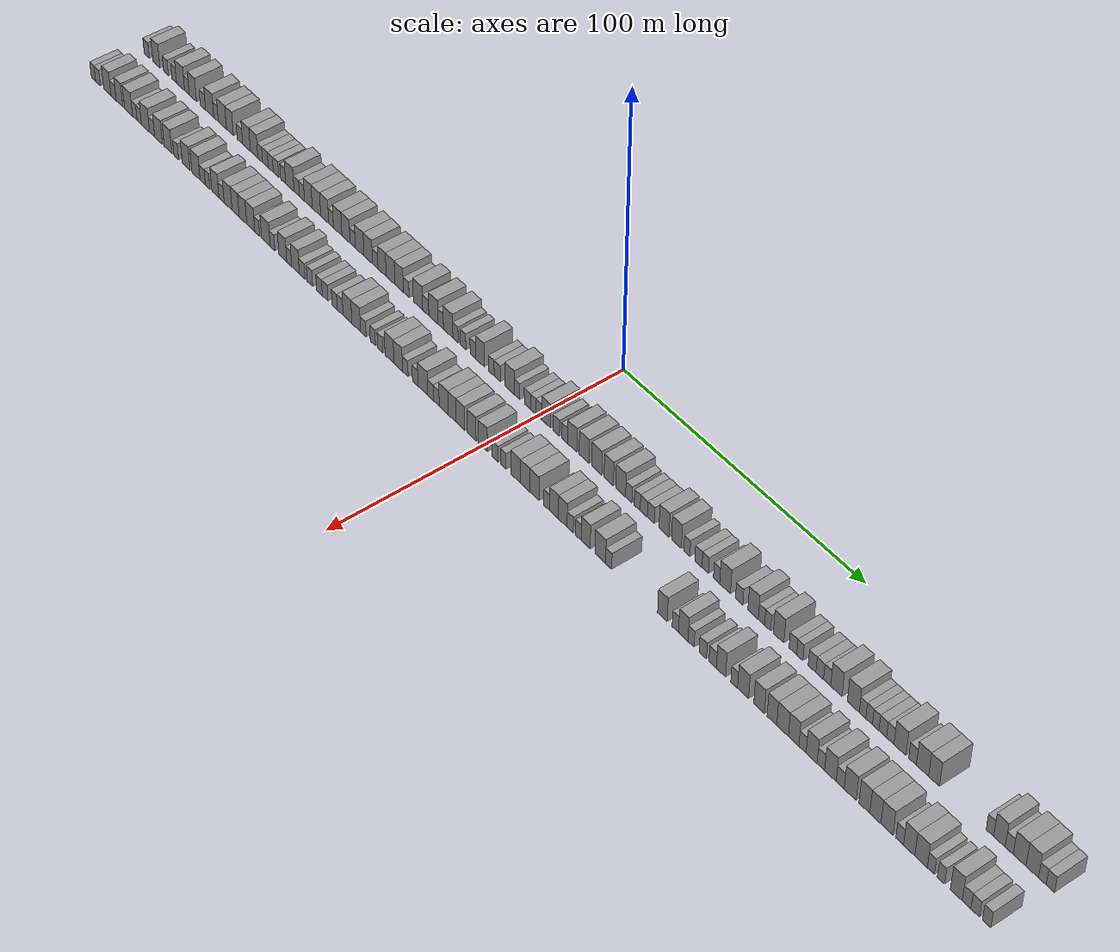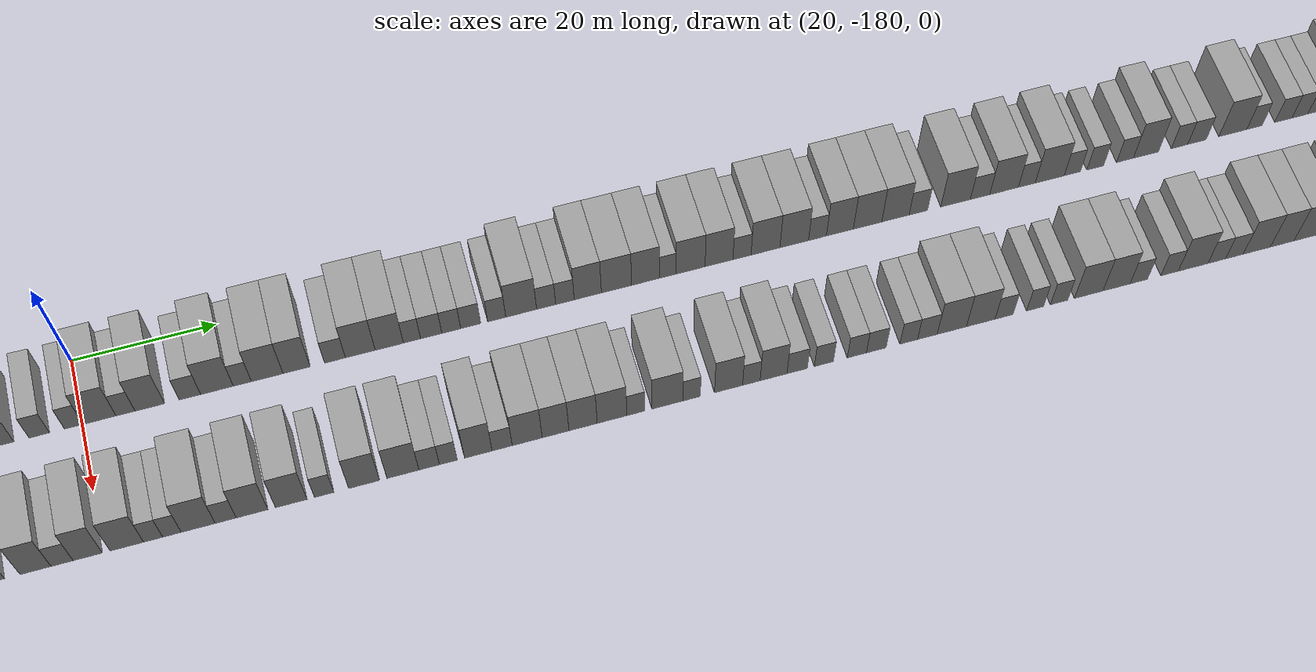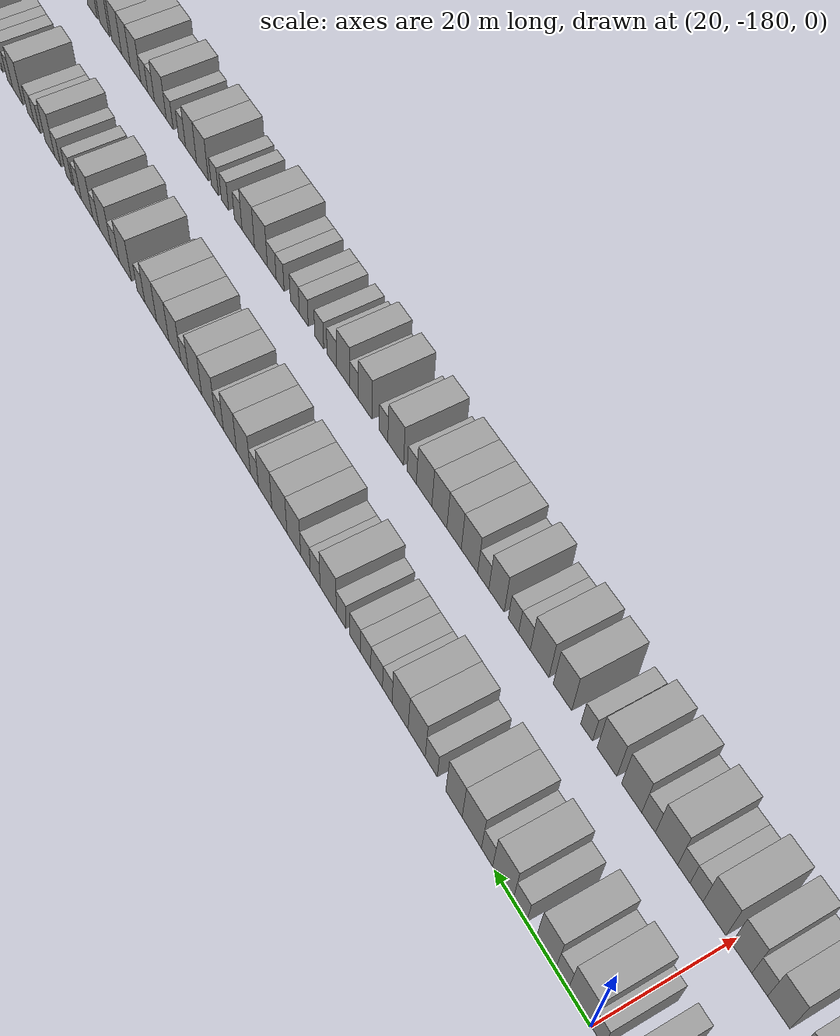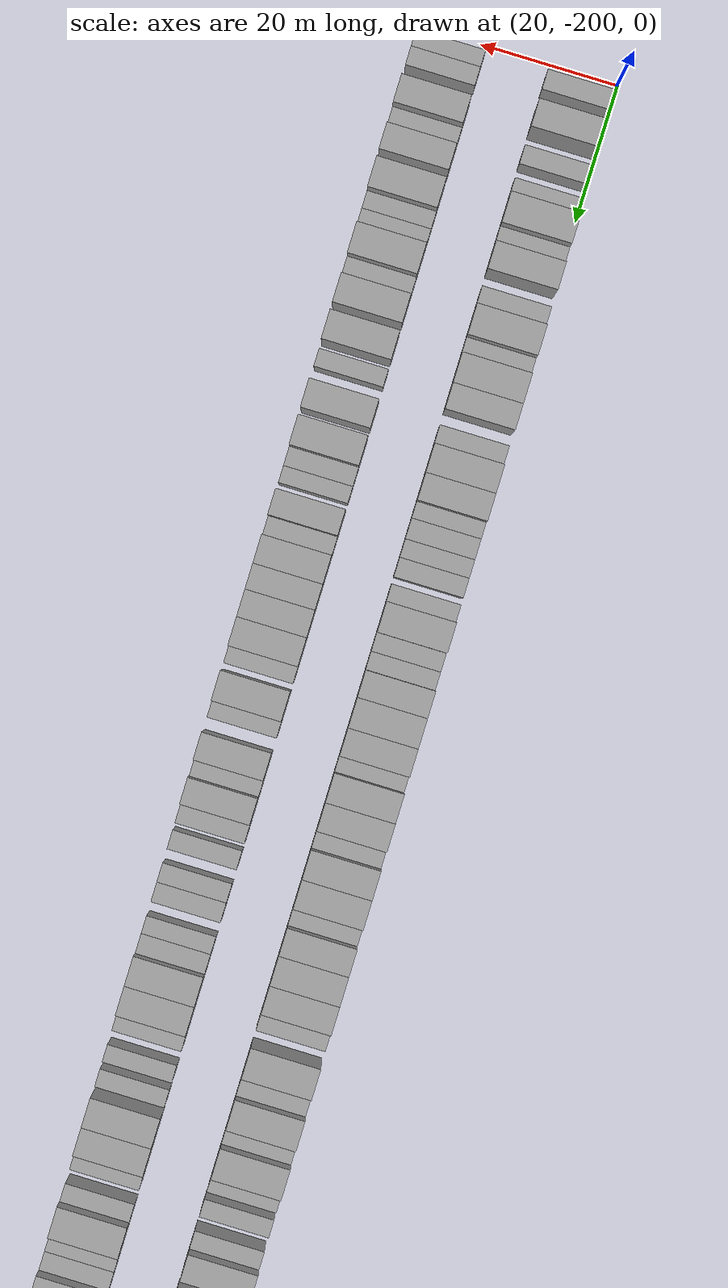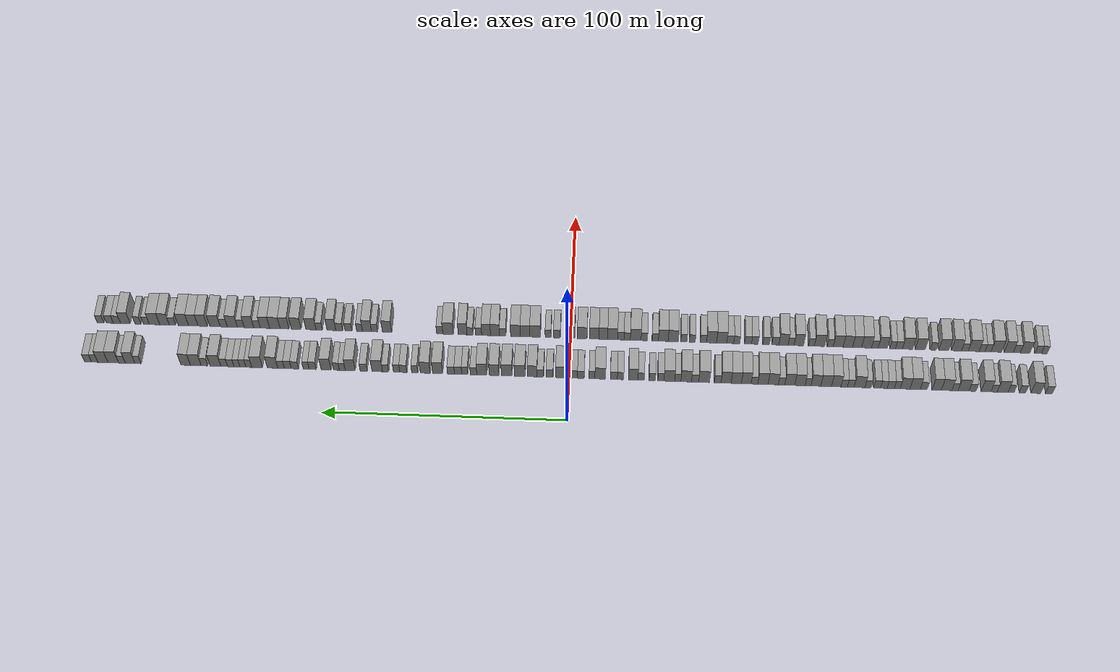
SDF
<sdf version="1.6">
 <world name="default">
  <scene>
   <sky><clouds><speed>12</speed></clouds></sky>
   <ambient>0.4 0.4 0.4 1</ambient>
   <background>0.7 0.7 0.7 1</background>
   <shadows>1</shadows>
  </scene>
  <gravity>0 0 -9.8066</gravity>
  <magnetic_field>6e-06 2.3e-05 -4.2e-05</magnetic_field>
  <physics default="0" name="default_physics" type="ode">
   <ode>
    <solver>
     <type>quick</type>
     <iters>10</iters>
     <sor>1.0</sor>
     <use_dynamic_moi_rescaling>0</use_dynamic_moi_rescaling>
    </solver>
    <constraints>
     <cfm>0</cfm>
     <erp>0.2</erp>
     <contact_max_correcting_vel>100</contact_max_correcting_vel>
     <contact_surface_layer>0.001</contact_surface_layer>
    </constraints>
   </ode>
   <max_step_size>0.004</max_step_size>
   <real_time_factor>1</real_time_factor>
   <real_time_update_rate>250</real_time_update_rate>
  </physics>
  <light name="sun" type="directional">
   <pose>0 0 10 0 0 0</pose>
   <diffuse>0.8 0.8 0.8 1</diffuse>
   <specular>0.2 0.2 0.2 1</specular>
   <attenuation>
    <range>1000</range>
    <constant>0.9</constant>
    <linear>0.01</linear>
    <quadratic>0.001</quadratic>
   </attenuation>
   <direction>-0.5 0.1 -0.9</direction>
  </light>
  <model name="building_1">
   <static>1</static>
   <pose>25.0000 -196.5566 0 0.000000 0.000000 0.000000</pose>
   <link name="link">
    <pose>0 0 3.00 0 0 0</pose>
    <collision name="collision"><geometry><box><size>10.0000 2.8868 6.0000</size></box></geometry></collision>
    <visual name="visual">
     <cast_shadows>0</cast_shadows>
     <geometry><box><size>10.0000 2.8868 6.0000</size></box></geometry>
     <material>
      <script>
       <uri>model://grey_wall/materials/scripts</uri>
       <uri>model://grey_wall/materials/textures</uri>
       <name>vrc/grey_wall</name>
      </script>
     </material>
    </visual>
   </link>
  </model>
  <model name="building_2">
   <static>1</static>
   <pose>25.0000 -191.1254 0 0.000000 0.000000 0.000000</pose>
   <link name="link">
    <pose>0 0 4.50 0 0 0</pose>
    <collision name="collision"><geometry><box><size>10.0000 3.9757 9.0000</size></box></geometry></collision>
    <visual name="visual">
     <cast_shadows>0</cast_shadows>
     <geometry><box><size>10.0000 3.9757 9.0000</size></box></geometry>
     <material>
      <script>
       <uri>model://grey_wall/materials/scripts</uri>
       <uri>model://grey_wall/materials/textures</uri>
       <name>vrc/grey_wall</name>
      </script>
     </material>
    </visual>
   </link>
  </model>
  <model name="building_3">
   <static>1</static>
   <pose>25.0000 -185.7663 0 0.000000 0.000000 0.000000</pose>
   <link name="link">
    <pose>0 0 3.00 0 0 0</pose>
    <collision name="collision"><geometry><box><size>10.0000 2.7424 6.0000</size></box></geometry></collision>
    <visual name="visual">
     <cast_shadows>0</cast_shadows>
     <geometry><box><size>10.0000 2.7424 6.0000</size></box></geometry>
     <material>
      <script>
       <uri>model://grey_wall/materials/scripts</uri>
       <uri>model://grey_wall/materials/textures</uri>
       <name>vrc/grey_wall</name>
      </script>
     </material>
    </visual>
   </link>
  </model>
  <model name="building_4">
   <static>1</static>
   <pose>25.0000 -181.1472 0 0.000000 0.000000 0.000000</pose>
   <link name="link">
    <pose>0 0 3.00 0 0 0</pose>
    <collision name="collision"><geometry><box><size>10.0000 2.4958 6.0000</size></box></geometry></collision>
    <visual name="visual">
     <cast_shadows>0</cast_shadows>
     <geometry><box><size>10.0000 2.4958 6.0000</size></box></geometry>
     <material>
      <script>
       <uri>model://grey_wall/materials/scripts</uri>
       <uri>model://grey_wall/materials/textures</uri>
       <name>vrc/grey_wall</name>
      </script>
     </material>
    </visual>
   </link>
  </model>
  <model name="building_5">
   <static>1</static>
   <pose>25.0000 -177.6643 0 0.000000 0.000000 0.000000</pose>
   <link name="link">
    <pose>0 0 4.50 0 0 0</pose>
    <collision name="collision"><geometry><box><size>10.0000 4.4701 9.0000</size></box></geometry></collision>
    <visual name="visual">
     <cast_shadows>0</cast_shadows>
     <geometry><box><size>10.0000 4.4701 9.0000</size></box></geometry>
     <material>
      <script>
       <uri>model://grey_wall/materials/scripts</uri>
       <uri>model://grey_wall/materials/textures</uri>
       <name>vrc/grey_wall</name>
      </script>
     </material>
    </visual>
   </link>
  </model>
  <model name="building_6">
   <static>1</static>
   <pose>25.0000 -174.1465 0 0.000000 0.000000 0.000000</pose>
   <link name="link">
    <pose>0 0 3.00 0 0 0</pose>
    <collision name="collision"><geometry><box><size>10.0000 2.5654 6.0000</size></box></geometry></collision>
    <visual name="visual">
     <cast_shadows>0</cast_shadows>
     <geometry><box><size>10.0000 2.5654 6.0000</size></box></geometry>
     <material>
      <script>
       <uri>model://grey_wall/materials/scripts</uri>
       <uri>model://grey_wall/materials/textures</uri>
       <name>vrc/grey_wall</name>
      </script>
     </material>
    </visual>
   </link>
  </model>
  <model name="building_7">
   <static>1</static>
   <pose>25.0000 -170.8509 0 0.000000 0.000000 0.000000</pose>
   <link name="link">
    <pose>0 0 4.50 0 0 0</pose>
    <collision name="collision"><geometry><box><size>10.0000 4.0258 9.0000</size></box></geometry></collision>
    <visual name="visual">
     <cast_shadows>0</cast_shadows>
     <geometry><box><size>10.0000 4.0258 9.0000</size></box></geometry>
     <material>
      <script>
       <uri>model://grey_wall/materials/scripts</uri>
       <uri>model://grey_wall/materials/textures</uri>
       <name>vrc/grey_wall</name>
      </script>
     </material>
    </visual>
   </link>
  </model>
  <model name="building_8">
   <static>1</static>
   <pose>25.0000 -165.3826 0 0.000000 0.000000 0.000000</pose>
   <link name="link">
    <pose>0 0 3.00 0 0 0</pose>
    <collision name="collision"><geometry><box><size>10.0000 2.9108 6.0000</size></box></geometry></collision>
    <visual name="visual">
     <cast_shadows>0</cast_shadows>
     <geometry><box><size>10.0000 2.9108 6.0000</size></box></geometry>
     <material>
      <script>
       <uri>model://grey_wall/materials/scripts</uri>
       <uri>model://grey_wall/materials/textures</uri>
       <name>vrc/grey_wall</name>
      </script>
     </material>
    </visual>
   </link>
  </model>
  <model name="building_9">
   <static>1</static>
   <pose>25.0000 -161.6923 0 0.000000 0.000000 0.000000</pose>
   <link name="link">
    <pose>0 0 4.50 0 0 0</pose>
    <collision name="collision"><geometry><box><size>10.0000 4.4697 9.0000</size></box></geometry></collision>
    <visual name="visual">
     <cast_shadows>0</cast_shadows>
     <geometry><box><size>10.0000 4.4697 9.0000</size></box></geometry>
     <material>
      <script>
       <uri>model://grey_wall/materials/scripts</uri>
       <uri>model://grey_wall/materials/textures</uri>
       <name>vrc/grey_wall</name>
      </script>
     </material>
    </visual>
   </link>
  </model>
  <model name="building_10">
   <static>1</static>
   <pose>25.0000 -158.2106 0 0.000000 0.000000 0.000000</pose>
   <link name="link">
    <pose>0 0 3.00 0 0 0</pose>
    <collision name="collision"><geometry><box><size>10.0000 2.4939 6.0000</size></box></geometry></collision>
    <visual name="visual">
     <cast_shadows>0</cast_shadows>
     <geometry><box><size>10.0000 2.4939 6.0000</size></box></geometry>
     <material>
      <script>
       <uri>model://grey_wall/materials/scripts</uri>
       <uri>model://grey_wall/materials/textures</uri>
       <name>vrc/grey_wall</name>
      </script>
     </material>
    </visual>
   </link>
  </model>
  <model name="building_11">
   <static>1</static>
   <pose>25.0000 -154.7831 0 0.000000 0.000000 0.000000</pose>
   <link name="link">
    <pose>0 0 4.50 0 0 0</pose>
    <collision name="collision"><geometry><box><size>10.0000 4.3610 9.0000</size></box></geometry></collision>
    <visual name="visual">
     <cast_shadows>0</cast_shadows>
     <geometry><box><size>10.0000 4.3610 9.0000</size></box></geometry>
     <material>
      <script>
       <uri>model://grey_wall/materials/scripts</uri>
       <uri>model://grey_wall/materials/textures</uri>
       <name>vrc/grey_wall</name>
      </script>
     </material>
    </visual>
   </link>
  </model>
  <model name="building_12">
   <static>1</static>
   <pose>25.0000 -150.7188 0 0.000000 0.000000 0.000000</pose>
   <link name="link">
    <pose>0 0 4.50 0 0 0</pose>
    <collision name="collision"><geometry><box><size>10.0000 3.7677 9.0000</size></box></geometry></collision>
    <visual name="visual">
     <cast_shadows>0</cast_shadows>
     <geometry><box><size>10.0000 3.7677 9.0000</size></box></geometry>
     <material>
      <script>
       <uri>model://grey_wall/materials/scripts</uri>
       <uri>model://grey_wall/materials/textures</uri>
       <name>vrc/grey_wall</name>
      </script>
     </material>
    </visual>
   </link>
  </model>
  <model name="building_13">
   <static>1</static>
   <pose>25.0000 -145.3944 0 0.000000 0.000000 0.000000</pose>
   <link name="link">
    <pose>0 0 3.00 0 0 0</pose>
    <collision name="collision"><geometry><box><size>10.0000 2.8811 6.0000</size></box></geometry></collision>
    <visual name="visual">
     <cast_shadows>0</cast_shadows>
     <geometry><box><size>10.0000 2.8811 6.0000</size></box></geometry>
     <material>
      <script>
       <uri>model://grey_wall/materials/scripts</uri>
       <uri>model://grey_wall/materials/textures</uri>
       <name>vrc/grey_wall</name>
      </script>
     </material>
    </visual>
   </link>
  </model>
  <model name="building_14">
   <static>1</static>
   <pose>25.0000 -141.8733 0 0.000000 0.000000 0.000000</pose>
   <link name="link">
    <pose>0 0 4.50 0 0 0</pose>
    <collision name="collision"><geometry><box><size>10.0000 4.1610 9.0000</size></box></geometry></collision>
    <visual name="visual">
     <cast_shadows>0</cast_shadows>
     <geometry><box><size>10.0000 4.1610 9.0000</size></box></geometry>
     <material>
      <script>
       <uri>model://grey_wall/materials/scripts</uri>
       <uri>model://grey_wall/materials/textures</uri>
       <name>vrc/grey_wall</name>
      </script>
     </material>
    </visual>
   </link>
  </model>
  <model name="building_15">
   <static>1</static>
   <pose>25.0000 -137.8103 0 0.000000 0.000000 0.000000</pose>
   <link name="link">
    <pose>0 0 4.50 0 0 0</pose>
    <collision name="collision"><geometry><box><size>10.0000 3.9649 9.0000</size></box></geometry></collision>
    <visual name="visual">
     <cast_shadows>0</cast_shadows>
     <geometry><box><size>10.0000 3.9649 9.0000</size></box></geometry>
     <material>
      <script>
       <uri>model://grey_wall/materials/scripts</uri>
       <uri>model://grey_wall/materials/textures</uri>
       <name>vrc/grey_wall</name>
      </script>
     </material>
    </visual>
   </link>
  </model>
  <model name="building_16">
   <static>1</static>
   <pose>25.0000 -134.6225 0 0.000000 0.000000 0.000000</pose>
   <link name="link">
    <pose>0 0 3.00 0 0 0</pose>
    <collision name="collision"><geometry><box><size>10.0000 2.4107 6.0000</size></box></geometry></collision>
    <visual name="visual">
     <cast_shadows>0</cast_shadows>
     <geometry><box><size>10.0000 2.4107 6.0000</size></box></geometry>
     <material>
      <script>
       <uri>model://grey_wall/materials/scripts</uri>
       <uri>model://grey_wall/materials/textures</uri>
       <name>vrc/grey_wall</name>
      </script>
     </material>
    </visual>
   </link>
  </model>
  <model name="building_17">
   <static>1</static>
   <pose>25.0000 -131.9212 0 0.000000 0.000000 0.000000</pose>
   <link name="link">
    <pose>0 0 3.00 0 0 0</pose>
    <collision name="collision"><geometry><box><size>10.0000 2.9920 6.0000</size></box></geometry></collision>
    <visual name="visual">
     <cast_shadows>0</cast_shadows>
     <geometry><box><size>10.0000 2.9920 6.0000</size></box></geometry>
     <material>
      <script>
       <uri>model://grey_wall/materials/scripts</uri>
       <uri>model://grey_wall/materials/textures</uri>
       <name>vrc/grey_wall</name>
      </script>
     </material>
    </visual>
   </link>
  </model>
  <model name="building_18">
   <static>1</static>
   <pose>25.0000 -129.0962 0 0.000000 0.000000 0.000000</pose>
   <link name="link">
    <pose>0 0 3.00 0 0 0</pose>
    <collision name="collision"><geometry><box><size>10.0000 2.6580 6.0000</size></box></geometry></collision>
    <visual name="visual">
     <cast_shadows>0</cast_shadows>
     <geometry><box><size>10.0000 2.6580 6.0000</size></box></geometry>
     <material>
      <script>
       <uri>model://grey_wall/materials/scripts</uri>
       <uri>model://grey_wall/materials/textures</uri>
       <name>vrc/grey_wall</name>
      </script>
     </material>
    </visual>
   </link>
  </model>
  <model name="building_19">
   <static>1</static>
   <pose>25.0000 -126.3533 0 0.000000 0.000000 0.000000</pose>
   <link name="link">
    <pose>0 0 3.00 0 0 0</pose>
    <collision name="collision"><geometry><box><size>10.0000 2.8278 6.0000</size></box></geometry></collision>
    <visual name="visual">
     <cast_shadows>0</cast_shadows>
     <geometry><box><size>10.0000 2.8278 6.0000</size></box></geometry>
     <material>
      <script>
       <uri>model://grey_wall/materials/scripts</uri>
       <uri>model://grey_wall/materials/textures</uri>
       <name>vrc/grey_wall</name>
      </script>
     </material>
    </visual>
   </link>
  </model>
  <model name="building_20">
   <static>1</static>
   <pose>25.0000 -122.6605 0 0.000000 0.000000 0.000000</pose>
   <link name="link">
    <pose>0 0 3.00 0 0 0</pose>
    <collision name="collision"><geometry><box><size>10.0000 2.5579 6.0000</size></box></geometry></collision>
    <visual name="visual">
     <cast_shadows>0</cast_shadows>
     <geometry><box><size>10.0000 2.5579 6.0000</size></box></geometry>
     <material>
      <script>
       <uri>model://grey_wall/materials/scripts</uri>
       <uri>model://grey_wall/materials/textures</uri>
       <name>vrc/grey_wall</name>
      </script>
     </material>
    </visual>
   </link>
  </model>
  <model name="building_21">
   <static>1</static>
   <pose>25.0000 -119.1797 0 0.000000 0.000000 0.000000</pose>
   <link name="link">
    <pose>0 0 4.50 0 0 0</pose>
    <collision name="collision"><geometry><box><size>10.0000 4.4037 9.0000</size></box></geometry></collision>
    <visual name="visual">
     <cast_shadows>0</cast_shadows>
     <geometry><box><size>10.0000 4.4037 9.0000</size></box></geometry>
     <material>
      <script>
       <uri>model://grey_wall/materials/scripts</uri>
       <uri>model://grey_wall/materials/textures</uri>
       <name>vrc/grey_wall</name>
      </script>
     </material>
    </visual>
   </link>
  </model>
  <model name="building_22">
   <static>1</static>
   <pose>25.0000 -115.6158 0 0.000000 0.000000 0.000000</pose>
   <link name="link">
    <pose>0 0 3.00 0 0 0</pose>
    <collision name="collision"><geometry><box><size>10.0000 2.7241 6.0000</size></box></geometry></collision>
    <visual name="visual">
     <cast_shadows>0</cast_shadows>
     <geometry><box><size>10.0000 2.7241 6.0000</size></box></geometry>
     <material>
      <script>
       <uri>model://grey_wall/materials/scripts</uri>
       <uri>model://grey_wall/materials/textures</uri>
       <name>vrc/grey_wall</name>
      </script>
     </material>
    </visual>
   </link>
  </model>
  <model name="building_23">
   <static>1</static>
   <pose>25.0000 -112.9241 0 0.000000 0.000000 0.000000</pose>
   <link name="link">
    <pose>0 0 3.00 0 0 0</pose>
    <collision name="collision"><geometry><box><size>10.0000 2.6591 6.0000</size></box></geometry></collision>
    <visual name="visual">
     <cast_shadows>0</cast_shadows>
     <geometry><box><size>10.0000 2.6591 6.0000</size></box></geometry>
     <material>
      <script>
       <uri>model://grey_wall/materials/scripts</uri>
       <uri>model://grey_wall/materials/textures</uri>
       <name>vrc/grey_wall</name>
      </script>
     </material>
    </visual>
   </link>
  </model>
  <model name="building_24">
   <static>1</static>
   <pose>25.0000 -109.6383 0 0.000000 0.000000 0.000000</pose>
   <link name="link">
    <pose>0 0 4.50 0 0 0</pose>
    <collision name="collision"><geometry><box><size>10.0000 3.9124 9.0000</size></box></geometry></collision>
    <visual name="visual">
     <cast_shadows>0</cast_shadows>
     <geometry><box><size>10.0000 3.9124 9.0000</size></box></geometry>
     <material>
      <script>
       <uri>model://grey_wall/materials/scripts</uri>
       <uri>model://grey_wall/materials/textures</uri>
       <name>vrc/grey_wall</name>
      </script>
     </material>
    </visual>
   </link>
  </model>
  <model name="building_25">
   <static>1</static>
   <pose>25.0000 -105.5020 0 0.000000 0.000000 0.000000</pose>
   <link name="link">
    <pose>0 0 4.50 0 0 0</pose>
    <collision name="collision"><geometry><box><size>10.0000 4.3603 9.0000</size></box></geometry></collision>
    <visual name="visual">
     <cast_shadows>0</cast_shadows>
     <geometry><box><size>10.0000 4.3603 9.0000</size></box></geometry>
     <material>
      <script>
       <uri>model://grey_wall/materials/scripts</uri>
       <uri>model://grey_wall/materials/textures</uri>
       <name>vrc/grey_wall</name>
      </script>
     </material>
    </visual>
   </link>
  </model>
  <model name="building_26">
   <static>1</static>
   <pose>25.0000 -101.3119 0 0.000000 0.000000 0.000000</pose>
   <link name="link">
    <pose>0 0 4.50 0 0 0</pose>
    <collision name="collision"><geometry><box><size>10.0000 4.0201 9.0000</size></box></geometry></collision>
    <visual name="visual">
     <cast_shadows>0</cast_shadows>
     <geometry><box><size>10.0000 4.0201 9.0000</size></box></geometry>
     <material>
      <script>
       <uri>model://grey_wall/materials/scripts</uri>
       <uri>model://grey_wall/materials/textures</uri>
       <name>vrc/grey_wall</name>
      </script>
     </material>
    </visual>
   </link>
  </model>
  <model name="building_27">
   <static>1</static>
   <pose>25.0000 -98.0989 0 0.000000 0.000000 0.000000</pose>
   <link name="link">
    <pose>0 0 3.00 0 0 0</pose>
    <collision name="collision"><geometry><box><size>10.0000 2.4057 6.0000</size></box></geometry></collision>
    <visual name="visual">
     <cast_shadows>0</cast_shadows>
     <geometry><box><size>10.0000 2.4057 6.0000</size></box></geometry>
     <material>
      <script>
       <uri>model://grey_wall/materials/scripts</uri>
       <uri>model://grey_wall/materials/textures</uri>
       <name>vrc/grey_wall</name>
      </script>
     </material>
    </visual>
   </link>
  </model>
  <model name="building_28">
   <static>1</static>
   <pose>25.0000 -94.7731 0 0.000000 0.000000 0.000000</pose>
   <link name="link">
    <pose>0 0 4.50 0 0 0</pose>
    <collision name="collision"><geometry><box><size>10.0000 4.2459 9.0000</size></box></geometry></collision>
    <visual name="visual">
     <cast_shadows>0</cast_shadows>
     <geometry><box><size>10.0000 4.2459 9.0000</size></box></geometry>
     <material>
      <script>
       <uri>model://grey_wall/materials/scripts</uri>
       <uri>model://grey_wall/materials/textures</uri>
       <name>vrc/grey_wall</name>
      </script>
     </material>
    </visual>
   </link>
  </model>
  <model name="building_29">
   <static>1</static>
   <pose>25.0000 -90.6110 0 0.000000 0.000000 0.000000</pose>
   <link name="link">
    <pose>0 0 4.50 0 0 0</pose>
    <collision name="collision"><geometry><box><size>10.0000 4.0784 9.0000</size></box></geometry></collision>
    <visual name="visual">
     <cast_shadows>0</cast_shadows>
     <geometry><box><size>10.0000 4.0784 9.0000</size></box></geometry>
     <material>
      <script>
       <uri>model://grey_wall/materials/scripts</uri>
       <uri>model://grey_wall/materials/textures</uri>
       <name>vrc/grey_wall</name>
      </script>
     </material>
    </visual>
   </link>
  </model>
  <model name="building_30">
   <static>1</static>
   <pose>25.0000 -87.2461 0 0.000000 0.000000 0.000000</pose>
   <link name="link">
    <pose>0 0 3.00 0 0 0</pose>
    <collision name="collision"><geometry><box><size>10.0000 2.6515 6.0000</size></box></geometry></collision>
    <visual name="visual">
     <cast_shadows>0</cast_shadows>
     <geometry><box><size>10.0000 2.6515 6.0000</size></box></geometry>
     <material>
      <script>
       <uri>model://grey_wall/materials/scripts</uri>
       <uri>model://grey_wall/materials/textures</uri>
       <name>vrc/grey_wall</name>
      </script>
     </material>
    </visual>
   </link>
  </model>
  <model name="building_31">
   <static>1</static>
   <pose>25.0000 -83.7917 0 0.000000 0.000000 0.000000</pose>
   <link name="link">
    <pose>0 0 4.50 0 0 0</pose>
    <collision name="collision"><geometry><box><size>10.0000 4.2573 9.0000</size></box></geometry></collision>
    <visual name="visual">
     <cast_shadows>0</cast_shadows>
     <geometry><box><size>10.0000 4.2573 9.0000</size></box></geometry>
     <material>
      <script>
       <uri>model://grey_wall/materials/scripts</uri>
       <uri>model://grey_wall/materials/textures</uri>
       <name>vrc/grey_wall</name>
      </script>
     </material>
    </visual>
   </link>
  </model>
  <model name="building_32">
   <static>1</static>
   <pose>25.0000 -79.5484 0 0.000000 0.000000 0.000000</pose>
   <link name="link">
    <pose>0 0 4.50 0 0 0</pose>
    <collision name="collision"><geometry><box><size>10.0000 4.2294 9.0000</size></box></geometry></collision>
    <visual name="visual">
     <cast_shadows>0</cast_shadows>
     <geometry><box><size>10.0000 4.2294 9.0000</size></box></geometry>
     <material>
      <script>
       <uri>model://grey_wall/materials/scripts</uri>
       <uri>model://grey_wall/materials/textures</uri>
       <name>vrc/grey_wall</name>
      </script>
     </material>
    </visual>
   </link>
  </model>
  <model name="building_33">
   <static>1</static>
   <pose>25.0000 -76.1040 0 0.000000 0.000000 0.000000</pose>
   <link name="link">
    <pose>0 0 3.00 0 0 0</pose>
    <collision name="collision"><geometry><box><size>10.0000 2.6593 6.0000</size></box></geometry></collision>
    <visual name="visual">
     <cast_shadows>0</cast_shadows>
     <geometry><box><size>10.0000 2.6593 6.0000</size></box></geometry>
     <material>
      <script>
       <uri>model://grey_wall/materials/scripts</uri>
       <uri>model://grey_wall/materials/textures</uri>
       <name>vrc/grey_wall</name>
      </script>
     </material>
    </visual>
   </link>
  </model>
  <model name="building_34">
   <static>1</static>
   <pose>25.0000 -72.7724 0 0.000000 0.000000 0.000000</pose>
   <link name="link">
    <pose>0 0 4.50 0 0 0</pose>
    <collision name="collision"><geometry><box><size>10.0000 4.0040 9.0000</size></box></geometry></collision>
    <visual name="visual">
     <cast_shadows>0</cast_shadows>
     <geometry><box><size>10.0000 4.0040 9.0000</size></box></geometry>
     <material>
      <script>
       <uri>model://grey_wall/materials/scripts</uri>
       <uri>model://grey_wall/materials/textures</uri>
       <name>vrc/grey_wall</name>
      </script>
     </material>
    </visual>
   </link>
  </model>
  <model name="building_35">
   <static>1</static>
   <pose>25.0000 -68.6466 0 0.000000 0.000000 0.000000</pose>
   <link name="link">
    <pose>0 0 4.50 0 0 0</pose>
    <collision name="collision"><geometry><box><size>10.0000 4.2477 9.0000</size></box></geometry></collision>
    <visual name="visual">
     <cast_shadows>0</cast_shadows>
     <geometry><box><size>10.0000 4.2477 9.0000</size></box></geometry>
     <material>
      <script>
       <uri>model://grey_wall/materials/scripts</uri>
       <uri>model://grey_wall/materials/textures</uri>
       <name>vrc/grey_wall</name>
      </script>
     </material>
    </visual>
   </link>
  </model>
  <model name="building_36">
   <static>1</static>
   <pose>25.0000 -64.4709 0 0.000000 0.000000 0.000000</pose>
   <link name="link">
    <pose>0 0 4.50 0 0 0</pose>
    <collision name="collision"><geometry><box><size>10.0000 4.1037 9.0000</size></box></geometry></collision>
    <visual name="visual">
     <cast_shadows>0</cast_shadows>
     <geometry><box><size>10.0000 4.1037 9.0000</size></box></geometry>
     <material>
      <script>
       <uri>model://grey_wall/materials/scripts</uri>
       <uri>model://grey_wall/materials/textures</uri>
       <name>vrc/grey_wall</name>
      </script>
     </material>
    </visual>
   </link>
  </model>
  <model name="building_37">
   <static>1</static>
   <pose>25.0000 -61.0392 0 0.000000 0.000000 0.000000</pose>
   <link name="link">
    <pose>0 0 3.00 0 0 0</pose>
    <collision name="collision"><geometry><box><size>10.0000 2.7598 6.0000</size></box></geometry></collision>
    <visual name="visual">
     <cast_shadows>0</cast_shadows>
     <geometry><box><size>10.0000 2.7598 6.0000</size></box></geometry>
     <material>
      <script>
       <uri>model://grey_wall/materials/scripts</uri>
       <uri>model://grey_wall/materials/textures</uri>
       <name>vrc/grey_wall</name>
      </script>
     </material>
    </visual>
   </link>
  </model>
  <model name="building_38">
   <static>1</static>
   <pose>25.0000 -55.4257 0 0.000000 0.000000 0.000000</pose>
   <link name="link">
    <pose>0 0 4.50 0 0 0</pose>
    <collision name="collision"><geometry><box><size>10.0000 4.4671 9.0000</size></box></geometry></collision>
    <visual name="visual">
     <cast_shadows>0</cast_shadows>
     <geometry><box><size>10.0000 4.4671 9.0000</size></box></geometry>
     <material>
      <script>
       <uri>model://grey_wall/materials/scripts</uri>
       <uri>model://grey_wall/materials/textures</uri>
       <name>vrc/grey_wall</name>
      </script>
     </material>
    </visual>
   </link>
  </model>
  <model name="building_39">
   <static>1</static>
   <pose>25.0000 -51.7245 0 0.000000 0.000000 0.000000</pose>
   <link name="link">
    <pose>0 0 3.00 0 0 0</pose>
    <collision name="collision"><geometry><box><size>10.0000 2.9353 6.0000</size></box></geometry></collision>
    <visual name="visual">
     <cast_shadows>0</cast_shadows>
     <geometry><box><size>10.0000 2.9353 6.0000</size></box></geometry>
     <material>
      <script>
       <uri>model://grey_wall/materials/scripts</uri>
       <uri>model://grey_wall/materials/textures</uri>
       <name>vrc/grey_wall</name>
      </script>
     </material>
    </visual>
   </link>
  </model>
  <model name="building_40">
   <static>1</static>
   <pose>25.0000 -48.0767 0 0.000000 0.000000 0.000000</pose>
   <link name="link">
    <pose>0 0 4.50 0 0 0</pose>
    <collision name="collision"><geometry><box><size>10.0000 4.3602 9.0000</size></box></geometry></collision>
    <visual name="visual">
     <cast_shadows>0</cast_shadows>
     <geometry><box><size>10.0000 4.3602 9.0000</size></box></geometry>
     <material>
      <script>
       <uri>model://grey_wall/materials/scripts</uri>
       <uri>model://grey_wall/materials/textures</uri>
       <name>vrc/grey_wall</name>
      </script>
     </material>
    </visual>
   </link>
  </model>
  <model name="building_41">
   <static>1</static>
   <pose>25.0000 -44.6150 0 0.000000 0.000000 0.000000</pose>
   <link name="link">
    <pose>0 0 3.00 0 0 0</pose>
    <collision name="collision"><geometry><box><size>10.0000 2.5633 6.0000</size></box></geometry></collision>
    <visual name="visual">
     <cast_shadows>0</cast_shadows>
     <geometry><box><size>10.0000 2.5633 6.0000</size></box></geometry>
     <material>
      <script>
       <uri>model://grey_wall/materials/scripts</uri>
       <uri>model://grey_wall/materials/textures</uri>
       <name>vrc/grey_wall</name>
      </script>
     </material>
    </visual>
   </link>
  </model>
  <model name="building_42">
   <static>1</static>
   <pose>25.0000 -41.1133 0 0.000000 0.000000 0.000000</pose>
   <link name="link">
    <pose>0 0 4.50 0 0 0</pose>
    <collision name="collision"><geometry><box><size>10.0000 4.4400 9.0000</size></box></geometry></collision>
    <visual name="visual">
     <cast_shadows>0</cast_shadows>
     <geometry><box><size>10.0000 4.4400 9.0000</size></box></geometry>
     <material>
      <script>
       <uri>model://grey_wall/materials/scripts</uri>
       <uri>model://grey_wall/materials/textures</uri>
       <name>vrc/grey_wall</name>
      </script>
     </material>
    </visual>
   </link>
  </model>
  <model name="building_43">
   <static>1</static>
   <pose>25.0000 -37.6530 0 0.000000 0.000000 0.000000</pose>
   <link name="link">
    <pose>0 0 3.00 0 0 0</pose>
    <collision name="collision"><geometry><box><size>10.0000 2.4807 6.0000</size></box></geometry></collision>
    <visual name="visual">
     <cast_shadows>0</cast_shadows>
     <geometry><box><size>10.0000 2.4807 6.0000</size></box></geometry>
     <material>
      <script>
       <uri>model://grey_wall/materials/scripts</uri>
       <uri>model://grey_wall/materials/textures</uri>
       <name>vrc/grey_wall</name>
      </script>
     </material>
    </visual>
   </link>
  </model>
  <model name="building_44">
   <static>1</static>
   <pose>25.0000 -34.1270 0 0.000000 0.000000 0.000000</pose>
   <link name="link">
    <pose>0 0 3.00 0 0 0</pose>
    <collision name="collision"><geometry><box><size>10.0000 2.5712 6.0000</size></box></geometry></collision>
    <visual name="visual">
     <cast_shadows>0</cast_shadows>
     <geometry><box><size>10.0000 2.5712 6.0000</size></box></geometry>
     <material>
      <script>
       <uri>model://grey_wall/materials/scripts</uri>
       <uri>model://grey_wall/materials/textures</uri>
       <name>vrc/grey_wall</name>
      </script>
     </material>
    </visual>
   </link>
  </model>
  <model name="building_45">
   <static>1</static>
   <pose>25.0000 -29.5381 0 0.000000 0.000000 0.000000</pose>
   <link name="link">
    <pose>0 0 3.00 0 0 0</pose>
    <collision name="collision"><geometry><box><size>10.0000 2.6066 6.0000</size></box></geometry></collision>
    <visual name="visual">
     <cast_shadows>0</cast_shadows>
     <geometry><box><size>10.0000 2.6066 6.0000</size></box></geometry>
     <material>
      <script>
       <uri>model://grey_wall/materials/scripts</uri>
       <uri>model://grey_wall/materials/textures</uri>
       <name>vrc/grey_wall</name>
      </script>
     </material>
    </visual>
   </link>
  </model>
  <model name="building_46">
   <static>1</static>
   <pose>25.0000 -26.2901 0 0.000000 0.000000 0.000000</pose>
   <link name="link">
    <pose>0 0 4.50 0 0 0</pose>
    <collision name="collision"><geometry><box><size>10.0000 3.8896 9.0000</size></box></geometry></collision>
    <visual name="visual">
     <cast_shadows>0</cast_shadows>
     <geometry><box><size>10.0000 3.8896 9.0000</size></box></geometry>
     <material>
      <script>
       <uri>model://grey_wall/materials/scripts</uri>
       <uri>model://grey_wall/materials/textures</uri>
       <name>vrc/grey_wall</name>
      </script>
     </material>
    </visual>
   </link>
  </model>
  <model name="building_47">
   <static>1</static>
   <pose>25.0000 -21.0578 0 0.000000 0.000000 0.000000</pose>
   <link name="link">
    <pose>0 0 3.00 0 0 0</pose>
    <collision name="collision"><geometry><box><size>10.0000 2.5750 6.0000</size></box></geometry></collision>
    <visual name="visual">
     <cast_shadows>0</cast_shadows>
     <geometry><box><size>10.0000 2.5750 6.0000</size></box></geometry>
     <material>
      <script>
       <uri>model://grey_wall/materials/scripts</uri>
       <uri>model://grey_wall/materials/textures</uri>
       <name>vrc/grey_wall</name>
      </script>
     </material>
    </visual>
   </link>
  </model>
  <model name="building_48">
   <static>1</static>
   <pose>25.0000 -18.3398 0 0.000000 0.000000 0.000000</pose>
   <link name="link">
    <pose>0 0 3.00 0 0 0</pose>
    <collision name="collision"><geometry><box><size>10.0000 2.8611 6.0000</size></box></geometry></collision>
    <visual name="visual">
     <cast_shadows>0</cast_shadows>
     <geometry><box><size>10.0000 2.8611 6.0000</size></box></geometry>
     <material>
      <script>
       <uri>model://grey_wall/materials/scripts</uri>
       <uri>model://grey_wall/materials/textures</uri>
       <name>vrc/grey_wall</name>
      </script>
     </material>
    </visual>
   </link>
  </model>
  <model name="building_49">
   <static>1</static>
   <pose>25.0000 -12.7190 0 0.000000 0.000000 0.000000</pose>
   <link name="link">
    <pose>0 0 4.50 0 0 0</pose>
    <collision name="collision"><geometry><box><size>10.0000 4.3804 9.0000</size></box></geometry></collision>
    <visual name="visual">
     <cast_shadows>0</cast_shadows>
     <geometry><box><size>10.0000 4.3804 9.0000</size></box></geometry>
     <material>
      <script>
       <uri>model://grey_wall/materials/scripts</uri>
       <uri>model://grey_wall/materials/textures</uri>
       <name>vrc/grey_wall</name>
      </script>
     </material>
    </visual>
   </link>
  </model>
  <model name="building_50">
   <static>1</static>
   <pose>25.0000 -9.3267 0 0.000000 0.000000 0.000000</pose>
   <link name="link">
    <pose>0 0 3.00 0 0 0</pose>
    <collision name="collision"><geometry><box><size>10.0000 2.4043 6.0000</size></box></geometry></collision>
    <visual name="visual">
     <cast_shadows>0</cast_shadows>
     <geometry><box><size>10.0000 2.4043 6.0000</size></box></geometry>
     <material>
      <script>
       <uri>model://grey_wall/materials/scripts</uri>
       <uri>model://grey_wall/materials/textures</uri>
       <name>vrc/grey_wall</name>
      </script>
     </material>
    </visual>
   </link>
  </model>
  <model name="building_51">
   <static>1</static>
   <pose>25.0000 -4.7424 0 0.000000 0.000000 0.000000</pose>
   <link name="link">
    <pose>0 0 3.00 0 0 0</pose>
    <collision name="collision"><geometry><box><size>10.0000 2.7642 6.0000</size></box></geometry></collision>
    <visual name="visual">
     <cast_shadows>0</cast_shadows>
     <geometry><box><size>10.0000 2.7642 6.0000</size></box></geometry>
     <material>
      <script>
       <uri>model://grey_wall/materials/scripts</uri>
       <uri>model://grey_wall/materials/textures</uri>
       <name>vrc/grey_wall</name>
      </script>
     </material>
    </visual>
   </link>
  </model>
  <model name="building_52">
   <static>1</static>
   <pose>25.0000 -2.1201 0 0.000000 0.000000 0.000000</pose>
   <link name="link">
    <pose>0 0 3.00 0 0 0</pose>
    <collision name="collision"><geometry><box><size>10.0000 2.4804 6.0000</size></box></geometry></collision>
    <visual name="visual">
     <cast_shadows>0</cast_shadows>
     <geometry><box><size>10.0000 2.4804 6.0000</size></box></geometry>
     <material>
      <script>
       <uri>model://grey_wall/materials/scripts</uri>
       <uri>model://grey_wall/materials/textures</uri>
       <name>vrc/grey_wall</name>
      </script>
     </material>
    </visual>
   </link>
  </model>
  <model name="building_53">
   <static>1</static>
   <pose>25.0000 0.4747 0 0.000000 0.000000 0.000000</pose>
   <link name="link">
    <pose>0 0 3.00 0 0 0</pose>
    <collision name="collision"><geometry><box><size>10.0000 2.7091 6.0000</size></box></geometry></collision>
    <visual name="visual">
     <cast_shadows>0</cast_shadows>
     <geometry><box><size>10.0000 2.7091 6.0000</size></box></geometry>
     <material>
      <script>
       <uri>model://grey_wall/materials/scripts</uri>
       <uri>model://grey_wall/materials/textures</uri>
       <name>vrc/grey_wall</name>
      </script>
     </material>
    </visual>
   </link>
  </model>
  <model name="building_54">
   <static>1</static>
   <pose>25.0000 3.7525 0 0.000000 0.000000 0.000000</pose>
   <link name="link">
    <pose>0 0 4.50 0 0 0</pose>
    <collision name="collision"><geometry><box><size>10.0000 3.8465 9.0000</size></box></geometry></collision>
    <visual name="visual">
     <cast_shadows>0</cast_shadows>
     <geometry><box><size>10.0000 3.8465 9.0000</size></box></geometry>
     <material>
      <script>
       <uri>model://grey_wall/materials/scripts</uri>
       <uri>model://grey_wall/materials/textures</uri>
       <name>vrc/grey_wall</name>
      </script>
     </material>
    </visual>
   </link>
  </model>
  <model name="building_55">
   <static>1</static>
   <pose>25.0000 8.1223 0 0.000000 0.000000 0.000000</pose>
   <link name="link">
    <pose>0 0 3.00 0 0 0</pose>
    <collision name="collision"><geometry><box><size>10.0000 2.8932 6.0000</size></box></geometry></collision>
    <visual name="visual">
     <cast_shadows>0</cast_shadows>
     <geometry><box><size>10.0000 2.8932 6.0000</size></box></geometry>
     <material>
      <script>
       <uri>model://grey_wall/materials/scripts</uri>
       <uri>model://grey_wall/materials/textures</uri>
       <name>vrc/grey_wall</name>
      </script>
     </material>
    </visual>
   </link>
  </model>
  <model name="building_56">
   <static>1</static>
   <pose>25.0000 11.9050 0 0.000000 0.000000 0.000000</pose>
   <link name="link">
    <pose>0 0 3.00 0 0 0</pose>
    <collision name="collision"><geometry><box><size>10.0000 2.6722 6.0000</size></box></geometry></collision>
    <visual name="visual">
     <cast_shadows>0</cast_shadows>
     <geometry><box><size>10.0000 2.6722 6.0000</size></box></geometry>
     <material>
      <script>
       <uri>model://grey_wall/materials/scripts</uri>
       <uri>model://grey_wall/materials/textures</uri>
       <name>vrc/grey_wall</name>
      </script>
     </material>
    </visual>
   </link>
  </model>
  <model name="building_57">
   <static>1</static>
   <pose>25.0000 15.2048 0 0.000000 0.000000 0.000000</pose>
   <link name="link">
    <pose>0 0 4.50 0 0 0</pose>
    <collision name="collision"><geometry><box><size>10.0000 3.9273 9.0000</size></box></geometry></collision>
    <visual name="visual">
     <cast_shadows>0</cast_shadows>
     <geometry><box><size>10.0000 3.9273 9.0000</size></box></geometry>
     <material>
      <script>
       <uri>model://grey_wall/materials/scripts</uri>
       <uri>model://grey_wall/materials/textures</uri>
       <name>vrc/grey_wall</name>
      </script>
     </material>
    </visual>
   </link>
  </model>
  <model name="building_58">
   <static>1</static>
   <pose>25.0000 20.3662 0 0.000000 0.000000 0.000000</pose>
   <link name="link">
    <pose>0 0 4.50 0 0 0</pose>
    <collision name="collision"><geometry><box><size>10.0000 4.3956 9.0000</size></box></geometry></collision>
    <visual name="visual">
     <cast_shadows>0</cast_shadows>
     <geometry><box><size>10.0000 4.3956 9.0000</size></box></geometry>
     <material>
      <script>
       <uri>model://grey_wall/materials/scripts</uri>
       <uri>model://grey_wall/materials/textures</uri>
       <name>vrc/grey_wall</name>
      </script>
     </material>
    </visual>
   </link>
  </model>
  <model name="building_59">
   <static>1</static>
   <pose>25.0000 25.7597 0 0.000000 0.000000 0.000000</pose>
   <link name="link">
    <pose>0 0 4.50 0 0 0</pose>
    <collision name="collision"><geometry><box><size>10.0000 4.3914 9.0000</size></box></geometry></collision>
    <visual name="visual">
     <cast_shadows>0</cast_shadows>
     <geometry><box><size>10.0000 4.3914 9.0000</size></box></geometry>
     <material>
      <script>
       <uri>model://grey_wall/materials/scripts</uri>
       <uri>model://grey_wall/materials/textures</uri>
       <name>vrc/grey_wall</name>
      </script>
     </material>
    </visual>
   </link>
  </model>
  <model name="building_60">
   <static>1</static>
   <pose>25.0000 30.9667 0 0.000000 0.000000 0.000000</pose>
   <link name="link">
    <pose>0 0 4.50 0 0 0</pose>
    <collision name="collision"><geometry><box><size>10.0000 4.0226 9.0000</size></box></geometry></collision>
    <visual name="visual">
     <cast_shadows>0</cast_shadows>
     <geometry><box><size>10.0000 4.0226 9.0000</size></box></geometry>
     <material>
      <script>
       <uri>model://grey_wall/materials/scripts</uri>
       <uri>model://grey_wall/materials/textures</uri>
       <name>vrc/grey_wall</name>
      </script>
     </material>
    </visual>
   </link>
  </model>
  <model name="building_61">
   <static>1</static>
   <pose>25.0000 36.0708 0 0.000000 0.000000 0.000000</pose>
   <link name="link">
    <pose>0 0 4.50 0 0 0</pose>
    <collision name="collision"><geometry><box><size>10.0000 4.1858 9.0000</size></box></geometry></collision>
    <visual name="visual">
     <cast_shadows>0</cast_shadows>
     <geometry><box><size>10.0000 4.1858 9.0000</size></box></geometry>
     <material>
      <script>
       <uri>model://grey_wall/materials/scripts</uri>
       <uri>model://grey_wall/materials/textures</uri>
       <name>vrc/grey_wall</name>
      </script>
     </material>
    </visual>
   </link>
  </model>
  <model name="building_62">
   <static>1</static>
   <pose>25.0000 39.4881 0 0.000000 0.000000 0.000000</pose>
   <link name="link">
    <pose>0 0 3.00 0 0 0</pose>
    <collision name="collision"><geometry><box><size>10.0000 2.6488 6.0000</size></box></geometry></collision>
    <visual name="visual">
     <cast_shadows>0</cast_shadows>
     <geometry><box><size>10.0000 2.6488 6.0000</size></box></geometry>
     <material>
      <script>
       <uri>model://grey_wall/materials/scripts</uri>
       <uri>model://grey_wall/materials/textures</uri>
       <name>vrc/grey_wall</name>
      </script>
     </material>
    </visual>
   </link>
  </model>
  <model name="building_63">
   <static>1</static>
   <pose>25.0000 43.0726 0 0.000000 0.000000 0.000000</pose>
   <link name="link">
    <pose>0 0 3.00 0 0 0</pose>
    <collision name="collision"><geometry><box><size>10.0000 2.5201 6.0000</size></box></geometry></collision>
    <visual name="visual">
     <cast_shadows>0</cast_shadows>
     <geometry><box><size>10.0000 2.5201 6.0000</size></box></geometry>
     <material>
      <script>
       <uri>model://grey_wall/materials/scripts</uri>
       <uri>model://grey_wall/materials/textures</uri>
       <name>vrc/grey_wall</name>
      </script>
     </material>
    </visual>
   </link>
  </model>
  <model name="building_64">
   <static>1</static>
   <pose>25.0000 45.8305 0 0.000000 0.000000 0.000000</pose>
   <link name="link">
    <pose>0 0 3.00 0 0 0</pose>
    <collision name="collision"><geometry><box><size>10.0000 2.9956 6.0000</size></box></geometry></collision>
    <visual name="visual">
     <cast_shadows>0</cast_shadows>
     <geometry><box><size>10.0000 2.9956 6.0000</size></box></geometry>
     <material>
      <script>
       <uri>model://grey_wall/materials/scripts</uri>
       <uri>model://grey_wall/materials/textures</uri>
       <name>vrc/grey_wall</name>
      </script>
     </material>
    </visual>
   </link>
  </model>
  <model name="building_65">
   <static>1</static>
   <pose>25.0000 48.7820 0 0.000000 0.000000 0.000000</pose>
   <link name="link">
    <pose>0 0 3.00 0 0 0</pose>
    <collision name="collision"><geometry><box><size>10.0000 2.9074 6.0000</size></box></geometry></collision>
    <visual name="visual">
     <cast_shadows>0</cast_shadows>
     <geometry><box><size>10.0000 2.9074 6.0000</size></box></geometry>
     <material>
      <script>
       <uri>model://grey_wall/materials/scripts</uri>
       <uri>model://grey_wall/materials/textures</uri>
       <name>vrc/grey_wall</name>
      </script>
     </material>
    </visual>
   </link>
  </model>
  <model name="building_66">
   <static>1</static>
   <pose>25.0000 54.3205 0 0.000000 0.000000 0.000000</pose>
   <link name="link">
    <pose>0 0 4.50 0 0 0</pose>
    <collision name="collision"><geometry><box><size>10.0000 4.1696 9.0000</size></box></geometry></collision>
    <visual name="visual">
     <cast_shadows>0</cast_shadows>
     <geometry><box><size>10.0000 4.1696 9.0000</size></box></geometry>
     <material>
      <script>
       <uri>model://grey_wall/materials/scripts</uri>
       <uri>model://grey_wall/materials/textures</uri>
       <name>vrc/grey_wall</name>
      </script>
     </material>
    </visual>
   </link>
  </model>
  <model name="building_67">
   <static>1</static>
   <pose>25.0000 59.4550 0 0.000000 0.000000 0.000000</pose>
   <link name="link">
    <pose>0 0 4.50 0 0 0</pose>
    <collision name="collision"><geometry><box><size>10.0000 4.0994 9.0000</size></box></geometry></collision>
    <visual name="visual">
     <cast_shadows>0</cast_shadows>
     <geometry><box><size>10.0000 4.0994 9.0000</size></box></geometry>
     <material>
      <script>
       <uri>model://grey_wall/materials/scripts</uri>
       <uri>model://grey_wall/materials/textures</uri>
       <name>vrc/grey_wall</name>
      </script>
     </material>
    </visual>
   </link>
  </model>
  <model name="building_68">
   <static>1</static>
   <pose>25.0000 63.7622 0 0.000000 0.000000 0.000000</pose>
   <link name="link">
    <pose>0 0 3.00 0 0 0</pose>
    <collision name="collision"><geometry><box><size>10.0000 2.5149 6.0000</size></box></geometry></collision>
    <visual name="visual">
     <cast_shadows>0</cast_shadows>
     <geometry><box><size>10.0000 2.5149 6.0000</size></box></geometry>
     <material>
      <script>
       <uri>model://grey_wall/materials/scripts</uri>
       <uri>model://grey_wall/materials/textures</uri>
       <name>vrc/grey_wall</name>
      </script>
     </material>
    </visual>
   </link>
  </model>
  <model name="building_69">
   <static>1</static>
   <pose>25.0000 68.4789 0 0.000000 0.000000 0.000000</pose>
   <link name="link">
    <pose>0 0 3.00 0 0 0</pose>
    <collision name="collision"><geometry><box><size>10.0000 2.9186 6.0000</size></box></geometry></collision>
    <visual name="visual">
     <cast_shadows>0</cast_shadows>
     <geometry><box><size>10.0000 2.9186 6.0000</size></box></geometry>
     <material>
      <script>
       <uri>model://grey_wall/materials/scripts</uri>
       <uri>model://grey_wall/materials/textures</uri>
       <name>vrc/grey_wall</name>
      </script>
     </material>
    </visual>
   </link>
  </model>
  <model name="building_70">
   <static>1</static>
   <pose>25.0000 71.2532 0 0.000000 0.000000 0.000000</pose>
   <link name="link">
    <pose>0 0 3.00 0 0 0</pose>
    <collision name="collision"><geometry><box><size>10.0000 2.6300 6.0000</size></box></geometry></collision>
    <visual name="visual">
     <cast_shadows>0</cast_shadows>
     <geometry><box><size>10.0000 2.6300 6.0000</size></box></geometry>
     <material>
      <script>
       <uri>model://grey_wall/materials/scripts</uri>
       <uri>model://grey_wall/materials/textures</uri>
       <name>vrc/grey_wall</name>
      </script>
     </material>
    </visual>
   </link>
  </model>
  <model name="building_71">
   <static>1</static>
   <pose>25.0000 75.8257 0 0.000000 0.000000 0.000000</pose>
   <link name="link">
    <pose>0 0 3.00 0 0 0</pose>
    <collision name="collision"><geometry><box><size>10.0000 2.5148 6.0000</size></box></geometry></collision>
    <visual name="visual">
     <cast_shadows>0</cast_shadows>
     <geometry><box><size>10.0000 2.5148 6.0000</size></box></geometry>
     <material>
      <script>
       <uri>model://grey_wall/materials/scripts</uri>
       <uri>model://grey_wall/materials/textures</uri>
       <name>vrc/grey_wall</name>
      </script>
     </material>
    </visual>
   </link>
  </model>
  <model name="building_72">
   <static>1</static>
   <pose>25.0000 79.2634 0 0.000000 0.000000 0.000000</pose>
   <link name="link">
    <pose>0 0 4.50 0 0 0</pose>
    <collision name="collision"><geometry><box><size>10.0000 4.3607 9.0000</size></box></geometry></collision>
    <visual name="visual">
     <cast_shadows>0</cast_shadows>
     <geometry><box><size>10.0000 4.3607 9.0000</size></box></geometry>
     <material>
      <script>
       <uri>model://grey_wall/materials/scripts</uri>
       <uri>model://grey_wall/materials/textures</uri>
       <name>vrc/grey_wall</name>
      </script>
     </material>
    </visual>
   </link>
  </model>
  <model name="building_73">
   <static>1</static>
   <pose>25.0000 84.9128 0 0.000000 0.000000 0.000000</pose>
   <link name="link">
    <pose>0 0 3.00 0 0 0</pose>
    <collision name="collision"><geometry><box><size>10.0000 2.9382 6.0000</size></box></geometry></collision>
    <visual name="visual">
     <cast_shadows>0</cast_shadows>
     <geometry><box><size>10.0000 2.9382 6.0000</size></box></geometry>
     <material>
      <script>
       <uri>model://grey_wall/materials/scripts</uri>
       <uri>model://grey_wall/materials/textures</uri>
       <name>vrc/grey_wall</name>
      </script>
     </material>
    </visual>
   </link>
  </model>
  <model name="building_74">
   <static>1</static>
   <pose>25.0000 90.4444 0 0.000000 0.000000 0.000000</pose>
   <link name="link">
    <pose>0 0 4.50 0 0 0</pose>
    <collision name="collision"><geometry><box><size>10.0000 4.1249 9.0000</size></box></geometry></collision>
    <visual name="visual">
     <cast_shadows>0</cast_shadows>
     <geometry><box><size>10.0000 4.1249 9.0000</size></box></geometry>
     <material>
      <script>
       <uri>model://grey_wall/materials/scripts</uri>
       <uri>model://grey_wall/materials/textures</uri>
       <name>vrc/grey_wall</name>
      </script>
     </material>
    </visual>
   </link>
  </model>
  <model name="building_75">
   <static>1</static>
   <pose>25.0000 93.7471 0 0.000000 0.000000 0.000000</pose>
   <link name="link">
    <pose>0 0 3.00 0 0 0</pose>
    <collision name="collision"><geometry><box><size>10.0000 2.4805 6.0000</size></box></geometry></collision>
    <visual name="visual">
     <cast_shadows>0</cast_shadows>
     <geometry><box><size>10.0000 2.4805 6.0000</size></box></geometry>
     <material>
      <script>
       <uri>model://grey_wall/materials/scripts</uri>
       <uri>model://grey_wall/materials/textures</uri>
       <name>vrc/grey_wall</name>
      </script>
     </material>
    </visual>
   </link>
  </model>
  <model name="building_76">
   <static>1</static>
   <pose>25.0000 96.1940 0 0.000000 0.000000 0.000000</pose>
   <link name="link">
    <pose>0 0 3.00 0 0 0</pose>
    <collision name="collision"><geometry><box><size>10.0000 2.4133 6.0000</size></box></geometry></collision>
    <visual name="visual">
     <cast_shadows>0</cast_shadows>
     <geometry><box><size>10.0000 2.4133 6.0000</size></box></geometry>
     <material>
      <script>
       <uri>model://grey_wall/materials/scripts</uri>
       <uri>model://grey_wall/materials/textures</uri>
       <name>vrc/grey_wall</name>
      </script>
     </material>
    </visual>
   </link>
  </model>
  <model name="building_77">
   <static>1</static>
   <pose>25.0000 100.4716 0 0.000000 0.000000 0.000000</pose>
   <link name="link">
    <pose>0 0 4.50 0 0 0</pose>
    <collision name="collision"><geometry><box><size>10.0000 4.1419 9.0000</size></box></geometry></collision>
    <visual name="visual">
     <cast_shadows>0</cast_shadows>
     <geometry><box><size>10.0000 4.1419 9.0000</size></box></geometry>
     <material>
      <script>
       <uri>model://grey_wall/materials/scripts</uri>
       <uri>model://grey_wall/materials/textures</uri>
       <name>vrc/grey_wall</name>
      </script>
     </material>
    </visual>
   </link>
  </model>
  <model name="building_78">
   <static>1</static>
   <pose>25.0000 106.0221 0 0.000000 0.000000 0.000000</pose>
   <link name="link">
    <pose>0 0 3.00 0 0 0</pose>
    <collision name="collision"><geometry><box><size>10.0000 2.9590 6.0000</size></box></geometry></collision>
    <visual name="visual">
     <cast_shadows>0</cast_shadows>
     <geometry><box><size>10.0000 2.9590 6.0000</size></box></geometry>
     <material>
      <script>
       <uri>model://grey_wall/materials/scripts</uri>
       <uri>model://grey_wall/materials/textures</uri>
       <name>vrc/grey_wall</name>
      </script>
     </material>
    </visual>
   </link>
  </model>
  <model name="building_79">
   <static>1</static>
   <pose>25.0000 108.7232 0 0.000000 0.000000 0.000000</pose>
   <link name="link">
    <pose>0 0 3.00 0 0 0</pose>
    <collision name="collision"><geometry><box><size>10.0000 2.4432 6.0000</size></box></geometry></collision>
    <visual name="visual">
     <cast_shadows>0</cast_shadows>
     <geometry><box><size>10.0000 2.4432 6.0000</size></box></geometry>
     <material>
      <script>
       <uri>model://grey_wall/materials/scripts</uri>
       <uri>model://grey_wall/materials/textures</uri>
       <name>vrc/grey_wall</name>
      </script>
     </material>
    </visual>
   </link>
  </model>
  <model name="building_80">
   <static>1</static>
   <pose>25.0000 113.4279 0 0.000000 0.000000 0.000000</pose>
   <link name="link">
    <pose>0 0 3.00 0 0 0</pose>
    <collision name="collision"><geometry><box><size>10.0000 2.9661 6.0000</size></box></geometry></collision>
    <visual name="visual">
     <cast_shadows>0</cast_shadows>
     <geometry><box><size>10.0000 2.9661 6.0000</size></box></geometry>
     <material>
      <script>
       <uri>model://grey_wall/materials/scripts</uri>
       <uri>model://grey_wall/materials/textures</uri>
       <name>vrc/grey_wall</name>
      </script>
     </material>
    </visual>
   </link>
  </model>
  <model name="building_81">
   <static>1</static>
   <pose>25.0000 116.3628 0 0.000000 0.000000 0.000000</pose>
   <link name="link">
    <pose>0 0 3.00 0 0 0</pose>
    <collision name="collision"><geometry><box><size>10.0000 2.9037 6.0000</size></box></geometry></collision>
    <visual name="visual">
     <cast_shadows>0</cast_shadows>
     <geometry><box><size>10.0000 2.9037 6.0000</size></box></geometry>
     <material>
      <script>
       <uri>model://grey_wall/materials/scripts</uri>
       <uri>model://grey_wall/materials/textures</uri>
       <name>vrc/grey_wall</name>
      </script>
     </material>
    </visual>
   </link>
  </model>
  <model name="building_82">
   <static>1</static>
   <pose>25.0000 119.1823 0 0.000000 0.000000 0.000000</pose>
   <link name="link">
    <pose>0 0 3.00 0 0 0</pose>
    <collision name="collision"><geometry><box><size>10.0000 2.7352 6.0000</size></box></geometry></collision>
    <visual name="visual">
     <cast_shadows>0</cast_shadows>
     <geometry><box><size>10.0000 2.7352 6.0000</size></box></geometry>
     <material>
      <script>
       <uri>model://grey_wall/materials/scripts</uri>
       <uri>model://grey_wall/materials/textures</uri>
       <name>vrc/grey_wall</name>
      </script>
     </material>
    </visual>
   </link>
  </model>
  <model name="building_83">
   <static>1</static>
   <pose>25.0000 122.6996 0 0.000000 0.000000 0.000000</pose>
   <link name="link">
    <pose>0 0 4.50 0 0 0</pose>
    <collision name="collision"><geometry><box><size>10.0000 4.2995 9.0000</size></box></geometry></collision>
    <visual name="visual">
     <cast_shadows>0</cast_shadows>
     <geometry><box><size>10.0000 4.2995 9.0000</size></box></geometry>
     <material>
      <script>
       <uri>model://grey_wall/materials/scripts</uri>
       <uri>model://grey_wall/materials/textures</uri>
       <name>vrc/grey_wall</name>
      </script>
     </material>
    </visual>
   </link>
  </model>
  <model name="building_84">
   <static>1</static>
   <pose>25.0000 129.0897 0 0.000000 0.000000 0.000000</pose>
   <link name="link">
    <pose>0 0 4.50 0 0 0</pose>
    <collision name="collision"><geometry><box><size>10.0000 4.4806 9.0000</size></box></geometry></collision>
    <visual name="visual">
     <cast_shadows>0</cast_shadows>
     <geometry><box><size>10.0000 4.4806 9.0000</size></box></geometry>
     <material>
      <script>
       <uri>model://grey_wall/materials/scripts</uri>
       <uri>model://grey_wall/materials/textures</uri>
       <name>vrc/grey_wall</name>
      </script>
     </material>
    </visual>
   </link>
  </model>
  <model name="building_85">
   <static>1</static>
   <pose>25.0000 132.5447 0 0.000000 0.000000 0.000000</pose>
   <link name="link">
    <pose>0 0 3.00 0 0 0</pose>
    <collision name="collision"><geometry><box><size>10.0000 2.4294 6.0000</size></box></geometry></collision>
    <visual name="visual">
     <cast_shadows>0</cast_shadows>
     <geometry><box><size>10.0000 2.4294 6.0000</size></box></geometry>
     <material>
      <script>
       <uri>model://grey_wall/materials/scripts</uri>
       <uri>model://grey_wall/materials/textures</uri>
       <name>vrc/grey_wall</name>
      </script>
     </material>
    </visual>
   </link>
  </model>
  <model name="building_86">
   <static>1</static>
   <pose>25.0000 134.9929 0 0.000000 0.000000 0.000000</pose>
   <link name="link">
    <pose>0 0 3.00 0 0 0</pose>
    <collision name="collision"><geometry><box><size>10.0000 2.4671 6.0000</size></box></geometry></collision>
    <visual name="visual">
     <cast_shadows>0</cast_shadows>
     <geometry><box><size>10.0000 2.4671 6.0000</size></box></geometry>
     <material>
      <script>
       <uri>model://grey_wall/materials/scripts</uri>
       <uri>model://grey_wall/materials/textures</uri>
       <name>vrc/grey_wall</name>
      </script>
     </material>
    </visual>
   </link>
  </model>
  <model name="building_87">
   <static>1</static>
   <pose>25.0000 137.4405 0 0.000000 0.000000 0.000000</pose>
   <link name="link">
    <pose>0 0 3.00 0 0 0</pose>
    <collision name="collision"><geometry><box><size>10.0000 2.4281 6.0000</size></box></geometry></collision>
    <visual name="visual">
     <cast_shadows>0</cast_shadows>
     <geometry><box><size>10.0000 2.4281 6.0000</size></box></geometry>
     <material>
      <script>
       <uri>model://grey_wall/materials/scripts</uri>
       <uri>model://grey_wall/materials/textures</uri>
       <name>vrc/grey_wall</name>
      </script>
     </material>
    </visual>
   </link>
  </model>
  <model name="building_88">
   <static>1</static>
   <pose>25.0000 140.0556 0 0.000000 0.000000 0.000000</pose>
   <link name="link">
    <pose>0 0 3.00 0 0 0</pose>
    <collision name="collision"><geometry><box><size>10.0000 2.8020 6.0000</size></box></geometry></collision>
    <visual name="visual">
     <cast_shadows>0</cast_shadows>
     <geometry><box><size>10.0000 2.8020 6.0000</size></box></geometry>
     <material>
      <script>
       <uri>model://grey_wall/materials/scripts</uri>
       <uri>model://grey_wall/materials/textures</uri>
       <name>vrc/grey_wall</name>
      </script>
     </material>
    </visual>
   </link>
  </model>
  <model name="building_89">
   <static>1</static>
   <pose>25.0000 142.8223 0 0.000000 0.000000 0.000000</pose>
   <link name="link">
    <pose>0 0 3.00 0 0 0</pose>
    <collision name="collision"><geometry><box><size>10.0000 2.7314 6.0000</size></box></geometry></collision>
    <visual name="visual">
     <cast_shadows>0</cast_shadows>
     <geometry><box><size>10.0000 2.7314 6.0000</size></box></geometry>
     <material>
      <script>
       <uri>model://grey_wall/materials/scripts</uri>
       <uri>model://grey_wall/materials/textures</uri>
       <name>vrc/grey_wall</name>
      </script>
     </material>
    </visual>
   </link>
  </model>
  <model name="building_90">
   <static>1</static>
   <pose>25.0000 146.3913 0 0.000000 0.000000 0.000000</pose>
   <link name="link">
    <pose>0 0 4.50 0 0 0</pose>
    <collision name="collision"><geometry><box><size>10.0000 4.4065 9.0000</size></box></geometry></collision>
    <visual name="visual">
     <cast_shadows>0</cast_shadows>
     <geometry><box><size>10.0000 4.4065 9.0000</size></box></geometry>
     <material>
      <script>
       <uri>model://grey_wall/materials/scripts</uri>
       <uri>model://grey_wall/materials/textures</uri>
       <name>vrc/grey_wall</name>
      </script>
     </material>
    </visual>
   </link>
  </model>
  <model name="building_91">
   <static>1</static>
   <pose>25.0000 150.9687 0 0.000000 0.000000 0.000000</pose>
   <link name="link">
    <pose>0 0 3.00 0 0 0</pose>
    <collision name="collision"><geometry><box><size>10.0000 2.7483 6.0000</size></box></geometry></collision>
    <visual name="visual">
     <cast_shadows>0</cast_shadows>
     <geometry><box><size>10.0000 2.7483 6.0000</size></box></geometry>
     <material>
      <script>
       <uri>model://grey_wall/materials/scripts</uri>
       <uri>model://grey_wall/materials/textures</uri>
       <name>vrc/grey_wall</name>
      </script>
     </material>
    </visual>
   </link>
  </model>
  <model name="building_92">
   <static>1</static>
   <pose>25.0000 154.5702 0 0.000000 0.000000 0.000000</pose>
   <link name="link">
    <pose>0 0 4.50 0 0 0</pose>
    <collision name="collision"><geometry><box><size>10.0000 4.4548 9.0000</size></box></geometry></collision>
    <visual name="visual">
     <cast_shadows>0</cast_shadows>
     <geometry><box><size>10.0000 4.4548 9.0000</size></box></geometry>
     <material>
      <script>
       <uri>model://grey_wall/materials/scripts</uri>
       <uri>model://grey_wall/materials/textures</uri>
       <name>vrc/grey_wall</name>
      </script>
     </material>
    </visual>
   </link>
  </model>
  <model name="building_93">
   <static>1</static>
   <pose>25.0000 158.7625 0 0.000000 0.000000 0.000000</pose>
   <link name="link">
    <pose>0 0 4.50 0 0 0</pose>
    <collision name="collision"><geometry><box><size>10.0000 3.9299 9.0000</size></box></geometry></collision>
    <visual name="visual">
     <cast_shadows>0</cast_shadows>
     <geometry><box><size>10.0000 3.9299 9.0000</size></box></geometry>
     <material>
      <script>
       <uri>model://grey_wall/materials/scripts</uri>
       <uri>model://grey_wall/materials/textures</uri>
       <name>vrc/grey_wall</name>
      </script>
     </material>
    </visual>
   </link>
  </model>
  <model name="building_94">
   <static>1</static>
   <pose>25.0000 178.5883 0 0.000000 0.000000 0.000000</pose>
   <link name="link">
    <pose>0 0 3.00 0 0 0</pose>
    <collision name="collision"><geometry><box><size>10.0000 2.5739 6.0000</size></box></geometry></collision>
    <visual name="visual">
     <cast_shadows>0</cast_shadows>
     <geometry><box><size>10.0000 2.5739 6.0000</size></box></geometry>
     <material>
      <script>
       <uri>model://grey_wall/materials/scripts</uri>
       <uri>model://grey_wall/materials/textures</uri>
       <name>vrc/grey_wall</name>
      </script>
     </material>
    </visual>
   </link>
  </model>
  <model name="building_95">
   <static>1</static>
   <pose>25.0000 181.8974 0 0.000000 0.000000 0.000000</pose>
   <link name="link">
    <pose>0 0 4.50 0 0 0</pose>
    <collision name="collision"><geometry><box><size>10.0000 4.0443 9.0000</size></box></geometry></collision>
    <visual name="visual">
     <cast_shadows>0</cast_shadows>
     <geometry><box><size>10.0000 4.0443 9.0000</size></box></geometry>
     <material>
      <script>
       <uri>model://grey_wall/materials/scripts</uri>
       <uri>model://grey_wall/materials/textures</uri>
       <name>vrc/grey_wall</name>
      </script>
     </material>
    </visual>
   </link>
  </model>
  <model name="building_96">
   <static>1</static>
   <pose>25.0000 185.3083 0 0.000000 0.000000 0.000000</pose>
   <link name="link">
    <pose>0 0 3.00 0 0 0</pose>
    <collision name="collision"><geometry><box><size>10.0000 2.7775 6.0000</size></box></geometry></collision>
    <visual name="visual">
     <cast_shadows>0</cast_shadows>
     <geometry><box><size>10.0000 2.7775 6.0000</size></box></geometry>
     <material>
      <script>
       <uri>model://grey_wall/materials/scripts</uri>
       <uri>model://grey_wall/materials/textures</uri>
       <name>vrc/grey_wall</name>
      </script>
     </material>
    </visual>
   </link>
  </model>
  <model name="building_97">
   <static>1</static>
   <pose>25.0000 188.8926 0 0.000000 0.000000 0.000000</pose>
   <link name="link">
    <pose>0 0 4.50 0 0 0</pose>
    <collision name="collision"><geometry><box><size>10.0000 4.3911 9.0000</size></box></geometry></collision>
    <visual name="visual">
     <cast_shadows>0</cast_shadows>
     <geometry><box><size>10.0000 4.3911 9.0000</size></box></geometry>
     <material>
      <script>
       <uri>model://grey_wall/materials/scripts</uri>
       <uri>model://grey_wall/materials/textures</uri>
       <name>vrc/grey_wall</name>
      </script>
     </material>
    </visual>
   </link>
  </model>
  <model name="building_98">
   <static>1</static>
   <pose>25.0000 193.2294 0 0.000000 0.000000 0.000000</pose>
   <link name="link">
    <pose>0 0 4.50 0 0 0</pose>
    <collision name="collision"><geometry><box><size>10.0000 4.2827 9.0000</size></box></geometry></collision>
    <visual name="visual">
     <cast_shadows>0</cast_shadows>
     <geometry><box><size>10.0000 4.2827 9.0000</size></box></geometry>
     <material>
      <script>
       <uri>model://grey_wall/materials/scripts</uri>
       <uri>model://grey_wall/materials/textures</uri>
       <name>vrc/grey_wall</name>
      </script>
     </material>
    </visual>
   </link>
  </model>
  <model name="building_99">
   <static>1</static>
   <pose>25.0000 196.6763 0 0.000000 0.000000 0.000000</pose>
   <link name="link">
    <pose>0 0 3.00 0 0 0</pose>
    <collision name="collision"><geometry><box><size>10.0000 2.6111 6.0000</size></box></geometry></collision>
    <visual name="visual">
     <cast_shadows>0</cast_shadows>
     <geometry><box><size>10.0000 2.6111 6.0000</size></box></geometry>
     <material>
      <script>
       <uri>model://grey_wall/materials/scripts</uri>
       <uri>model://grey_wall/materials/textures</uri>
       <name>vrc/grey_wall</name>
      </script>
     </material>
    </visual>
   </link>
  </model>
  <model name="building_100">
   <static>1</static>
   <pose>25.0000 199.4241 0 0.000000 0.000000 0.000000</pose>
   <link name="link">
    <pose>0 0 3.00 0 0 0</pose>
    <collision name="collision"><geometry><box><size>10.0000 2.8844 6.0000</size></box></geometry></collision>
    <visual name="visual">
     <cast_shadows>0</cast_shadows>
     <geometry><box><size>10.0000 2.8844 6.0000</size></box></geometry>
     <material>
      <script>
       <uri>model://grey_wall/materials/scripts</uri>
       <uri>model://grey_wall/materials/textures</uri>
       <name>vrc/grey_wall</name>
      </script>
     </material>
    </visual>
   </link>
  </model>
  <model name="building_101">
   <static>1</static>
   <pose>44.0000 -196.7867 0 0.000000 0.000000 0.000000</pose>
   <link name="link">
    <pose>0 0 3.00 0 0 0</pose>
    <collision name="collision"><geometry><box><size>10.0000 2.4267 6.0000</size></box></geometry></collision>
    <visual name="visual">
     <cast_shadows>0</cast_shadows>
     <geometry><box><size>10.0000 2.4267 6.0000</size></box></geometry>
     <material>
      <script>
       <uri>model://grey_wall/materials/scripts</uri>
       <uri>model://grey_wall/materials/textures</uri>
       <name>vrc/grey_wall</name>
      </script>
     </material>
    </visual>
   </link>
  </model>
  <model name="building_102">
   <static>1</static>
   <pose>44.0000 -194.2167 0 0.000000 0.000000 0.000000</pose>
   <link name="link">
    <pose>0 0 3.00 0 0 0</pose>
    <collision name="collision"><geometry><box><size>10.0000 2.7133 6.0000</size></box></geometry></collision>
    <visual name="visual">
     <cast_shadows>0</cast_shadows>
     <geometry><box><size>10.0000 2.7133 6.0000</size></box></geometry>
     <material>
      <script>
       <uri>model://grey_wall/materials/scripts</uri>
       <uri>model://grey_wall/materials/textures</uri>
       <name>vrc/grey_wall</name>
      </script>
     </material>
    </visual>
   </link>
  </model>
  <model name="building_103">
   <static>1</static>
   <pose>44.0000 -188.8506 0 0.000000 0.000000 0.000000</pose>
   <link name="link">
    <pose>0 0 4.50 0 0 0</pose>
    <collision name="collision"><geometry><box><size>10.0000 4.0188 9.0000</size></box></geometry></collision>
    <visual name="visual">
     <cast_shadows>0</cast_shadows>
     <geometry><box><size>10.0000 4.0188 9.0000</size></box></geometry>
     <material>
      <script>
       <uri>model://grey_wall/materials/scripts</uri>
       <uri>model://grey_wall/materials/textures</uri>
       <name>vrc/grey_wall</name>
      </script>
     </material>
    </visual>
   </link>
  </model>
  <model name="building_104">
   <static>1</static>
   <pose>44.0000 -185.4043 0 0.000000 0.000000 0.000000</pose>
   <link name="link">
    <pose>0 0 3.00 0 0 0</pose>
    <collision name="collision"><geometry><box><size>10.0000 2.8738 6.0000</size></box></geometry></collision>
    <visual name="visual">
     <cast_shadows>0</cast_shadows>
     <geometry><box><size>10.0000 2.8738 6.0000</size></box></geometry>
     <material>
      <script>
       <uri>model://grey_wall/materials/scripts</uri>
       <uri>model://grey_wall/materials/textures</uri>
       <name>vrc/grey_wall</name>
      </script>
     </material>
    </visual>
   </link>
  </model>
  <model name="building_105">
   <static>1</static>
   <pose>44.0000 -182.0628 0 0.000000 0.000000 0.000000</pose>
   <link name="link">
    <pose>0 0 4.50 0 0 0</pose>
    <collision name="collision"><geometry><box><size>10.0000 3.8092 9.0000</size></box></geometry></collision>
    <visual name="visual">
     <cast_shadows>0</cast_shadows>
     <geometry><box><size>10.0000 3.8092 9.0000</size></box></geometry>
     <material>
      <script>
       <uri>model://grey_wall/materials/scripts</uri>
       <uri>model://grey_wall/materials/textures</uri>
       <name>vrc/grey_wall</name>
      </script>
     </material>
    </visual>
   </link>
  </model>
  <model name="building_106">
   <static>1</static>
   <pose>44.0000 -176.9590 0 0.000000 0.000000 0.000000</pose>
   <link name="link">
    <pose>0 0 4.50 0 0 0</pose>
    <collision name="collision"><geometry><box><size>10.0000 4.3985 9.0000</size></box></geometry></collision>
    <visual name="visual">
     <cast_shadows>0</cast_shadows>
     <geometry><box><size>10.0000 4.3985 9.0000</size></box></geometry>
     <material>
      <script>
       <uri>model://grey_wall/materials/scripts</uri>
       <uri>model://grey_wall/materials/textures</uri>
       <name>vrc/grey_wall</name>
      </script>
     </material>
    </visual>
   </link>
  </model>
  <model name="building_107">
   <static>1</static>
   <pose>44.0000 -173.5028 0 0.000000 0.000000 0.000000</pose>
   <link name="link">
    <pose>0 0 3.00 0 0 0</pose>
    <collision name="collision"><geometry><box><size>10.0000 2.5139 6.0000</size></box></geometry></collision>
    <visual name="visual">
     <cast_shadows>0</cast_shadows>
     <geometry><box><size>10.0000 2.5139 6.0000</size></box></geometry>
     <material>
      <script>
       <uri>model://grey_wall/materials/scripts</uri>
       <uri>model://grey_wall/materials/textures</uri>
       <name>vrc/grey_wall</name>
      </script>
     </material>
    </visual>
   </link>
  </model>
  <model name="building_108">
   <static>1</static>
   <pose>44.0000 -171.0307 0 0.000000 0.000000 0.000000</pose>
   <link name="link">
    <pose>0 0 3.00 0 0 0</pose>
    <collision name="collision"><geometry><box><size>10.0000 2.4303 6.0000</size></box></geometry></collision>
    <visual name="visual">
     <cast_shadows>0</cast_shadows>
     <geometry><box><size>10.0000 2.4303 6.0000</size></box></geometry>
     <material>
      <script>
       <uri>model://grey_wall/materials/scripts</uri>
       <uri>model://grey_wall/materials/textures</uri>
       <name>vrc/grey_wall</name>
      </script>
     </material>
    </visual>
   </link>
  </model>
  <model name="building_109">
   <static>1</static>
   <pose>44.0000 -167.5669 0 0.000000 0.000000 0.000000</pose>
   <link name="link">
    <pose>0 0 4.50 0 0 0</pose>
    <collision name="collision"><geometry><box><size>10.0000 4.4973 9.0000</size></box></geometry></collision>
    <visual name="visual">
     <cast_shadows>0</cast_shadows>
     <geometry><box><size>10.0000 4.4973 9.0000</size></box></geometry>
     <material>
      <script>
       <uri>model://grey_wall/materials/scripts</uri>
       <uri>model://grey_wall/materials/textures</uri>
       <name>vrc/grey_wall</name>
      </script>
     </material>
    </visual>
   </link>
  </model>
  <model name="building_110">
   <static>1</static>
   <pose>44.0000 -163.9186 0 0.000000 0.000000 0.000000</pose>
   <link name="link">
    <pose>0 0 3.00 0 0 0</pose>
    <collision name="collision"><geometry><box><size>10.0000 2.7993 6.0000</size></box></geometry></collision>
    <visual name="visual">
     <cast_shadows>0</cast_shadows>
     <geometry><box><size>10.0000 2.7993 6.0000</size></box></geometry>
     <material>
      <script>
       <uri>model://grey_wall/materials/scripts</uri>
       <uri>model://grey_wall/materials/textures</uri>
       <name>vrc/grey_wall</name>
      </script>
     </material>
    </visual>
   </link>
  </model>
  <model name="building_111">
   <static>1</static>
   <pose>44.0000 -160.4133 0 0.000000 0.000000 0.000000</pose>
   <link name="link">
    <pose>0 0 4.50 0 0 0</pose>
    <collision name="collision"><geometry><box><size>10.0000 4.2114 9.0000</size></box></geometry></collision>
    <visual name="visual">
     <cast_shadows>0</cast_shadows>
     <geometry><box><size>10.0000 4.2114 9.0000</size></box></geometry>
     <material>
      <script>
       <uri>model://grey_wall/materials/scripts</uri>
       <uri>model://grey_wall/materials/textures</uri>
       <name>vrc/grey_wall</name>
      </script>
     </material>
    </visual>
   </link>
  </model>
  <model name="building_112">
   <static>1</static>
   <pose>44.0000 -155.1911 0 0.000000 0.000000 0.000000</pose>
   <link name="link">
    <pose>0 0 4.50 0 0 0</pose>
    <collision name="collision"><geometry><box><size>10.0000 4.2330 9.0000</size></box></geometry></collision>
    <visual name="visual">
     <cast_shadows>0</cast_shadows>
     <geometry><box><size>10.0000 4.2330 9.0000</size></box></geometry>
     <material>
      <script>
       <uri>model://grey_wall/materials/scripts</uri>
       <uri>model://grey_wall/materials/textures</uri>
       <name>vrc/grey_wall</name>
      </script>
     </material>
    </visual>
   </link>
  </model>
  <model name="building_113">
   <static>1</static>
   <pose>44.0000 -150.7769 0 0.000000 0.000000 0.000000</pose>
   <link name="link">
    <pose>0 0 3.00 0 0 0</pose>
    <collision name="collision"><geometry><box><size>10.0000 2.5955 6.0000</size></box></geometry></collision>
    <visual name="visual">
     <cast_shadows>0</cast_shadows>
     <geometry><box><size>10.0000 2.5955 6.0000</size></box></geometry>
     <material>
      <script>
       <uri>model://grey_wall/materials/scripts</uri>
       <uri>model://grey_wall/materials/textures</uri>
       <name>vrc/grey_wall</name>
      </script>
     </material>
    </visual>
   </link>
  </model>
  <model name="building_114">
   <static>1</static>
   <pose>44.0000 -145.3938 0 0.000000 0.000000 0.000000</pose>
   <link name="link">
    <pose>0 0 4.50 0 0 0</pose>
    <collision name="collision"><geometry><box><size>10.0000 4.1707 9.0000</size></box></geometry></collision>
    <visual name="visual">
     <cast_shadows>0</cast_shadows>
     <geometry><box><size>10.0000 4.1707 9.0000</size></box></geometry>
     <material>
      <script>
       <uri>model://grey_wall/materials/scripts</uri>
       <uri>model://grey_wall/materials/textures</uri>
       <name>vrc/grey_wall</name>
      </script>
     </material>
    </visual>
   </link>
  </model>
  <model name="building_115">
   <static>1</static>
   <pose>44.0000 -140.1387 0 0.000000 0.000000 0.000000</pose>
   <link name="link">
    <pose>0 0 4.50 0 0 0</pose>
    <collision name="collision"><geometry><box><size>10.0000 4.3393 9.0000</size></box></geometry></collision>
    <visual name="visual">
     <cast_shadows>0</cast_shadows>
     <geometry><box><size>10.0000 4.3393 9.0000</size></box></geometry>
     <material>
      <script>
       <uri>model://grey_wall/materials/scripts</uri>
       <uri>model://grey_wall/materials/textures</uri>
       <name>vrc/grey_wall</name>
      </script>
     </material>
    </visual>
   </link>
  </model>
  <model name="building_116">
   <static>1</static>
   <pose>44.0000 -136.5784 0 0.000000 0.000000 0.000000</pose>
   <link name="link">
    <pose>0 0 3.00 0 0 0</pose>
    <collision name="collision"><geometry><box><size>10.0000 2.7813 6.0000</size></box></geometry></collision>
    <visual name="visual">
     <cast_shadows>0</cast_shadows>
     <geometry><box><size>10.0000 2.7813 6.0000</size></box></geometry>
     <material>
      <script>
       <uri>model://grey_wall/materials/scripts</uri>
       <uri>model://grey_wall/materials/textures</uri>
       <name>vrc/grey_wall</name>
      </script>
     </material>
    </visual>
   </link>
  </model>
  <model name="building_117">
   <static>1</static>
   <pose>44.0000 -133.9641 0 0.000000 0.000000 0.000000</pose>
   <link name="link">
    <pose>0 0 3.00 0 0 0</pose>
    <collision name="collision"><geometry><box><size>10.0000 2.4475 6.0000</size></box></geometry></collision>
    <visual name="visual">
     <cast_shadows>0</cast_shadows>
     <geometry><box><size>10.0000 2.4475 6.0000</size></box></geometry>
     <material>
      <script>
       <uri>model://grey_wall/materials/scripts</uri>
       <uri>model://grey_wall/materials/textures</uri>
       <name>vrc/grey_wall</name>
      </script>
     </material>
    </visual>
   </link>
  </model>
  <model name="building_118">
   <static>1</static>
   <pose>44.0000 -129.8582 0 0.000000 0.000000 0.000000</pose>
   <link name="link">
    <pose>0 0 4.50 0 0 0</pose>
    <collision name="collision"><geometry><box><size>10.0000 3.7642 9.0000</size></box></geometry></collision>
    <visual name="visual">
     <cast_shadows>0</cast_shadows>
     <geometry><box><size>10.0000 3.7642 9.0000</size></box></geometry>
     <material>
      <script>
       <uri>model://grey_wall/materials/scripts</uri>
       <uri>model://grey_wall/materials/textures</uri>
       <name>vrc/grey_wall</name>
      </script>
     </material>
    </visual>
   </link>
  </model>
  <model name="building_119">
   <static>1</static>
   <pose>44.0000 -126.5897 0 0.000000 0.000000 0.000000</pose>
   <link name="link">
    <pose>0 0 3.00 0 0 0</pose>
    <collision name="collision"><geometry><box><size>10.0000 2.7729 6.0000</size></box></geometry></collision>
    <visual name="visual">
     <cast_shadows>0</cast_shadows>
     <geometry><box><size>10.0000 2.7729 6.0000</size></box></geometry>
     <material>
      <script>
       <uri>model://grey_wall/materials/scripts</uri>
       <uri>model://grey_wall/materials/textures</uri>
       <name>vrc/grey_wall</name>
      </script>
     </material>
    </visual>
   </link>
  </model>
  <model name="building_120">
   <static>1</static>
   <pose>44.0000 -123.1337 0 0.000000 0.000000 0.000000</pose>
   <link name="link">
    <pose>0 0 4.50 0 0 0</pose>
    <collision name="collision"><geometry><box><size>10.0000 4.1390 9.0000</size></box></geometry></collision>
    <visual name="visual">
     <cast_shadows>0</cast_shadows>
     <geometry><box><size>10.0000 4.1390 9.0000</size></box></geometry>
     <material>
      <script>
       <uri>model://grey_wall/materials/scripts</uri>
       <uri>model://grey_wall/materials/textures</uri>
       <name>vrc/grey_wall</name>
      </script>
     </material>
    </visual>
   </link>
  </model>
  <model name="building_121">
   <static>1</static>
   <pose>44.0000 -119.2107 0 0.000000 0.000000 0.000000</pose>
   <link name="link">
    <pose>0 0 4.50 0 0 0</pose>
    <collision name="collision"><geometry><box><size>10.0000 3.7071 9.0000</size></box></geometry></collision>
    <visual name="visual">
     <cast_shadows>0</cast_shadows>
     <geometry><box><size>10.0000 3.7071 9.0000</size></box></geometry>
     <material>
      <script>
       <uri>model://grey_wall/materials/scripts</uri>
       <uri>model://grey_wall/materials/textures</uri>
       <name>vrc/grey_wall</name>
      </script>
     </material>
    </visual>
   </link>
  </model>
  <model name="building_122">
   <static>1</static>
   <pose>44.0000 -115.3932 0 0.000000 0.000000 0.000000</pose>
   <link name="link">
    <pose>0 0 4.50 0 0 0</pose>
    <collision name="collision"><geometry><box><size>10.0000 3.9279 9.0000</size></box></geometry></collision>
    <visual name="visual">
     <cast_shadows>0</cast_shadows>
     <geometry><box><size>10.0000 3.9279 9.0000</size></box></geometry>
     <material>
      <script>
       <uri>model://grey_wall/materials/scripts</uri>
       <uri>model://grey_wall/materials/textures</uri>
       <name>vrc/grey_wall</name>
      </script>
     </material>
    </visual>
   </link>
  </model>
  <model name="building_123">
   <static>1</static>
   <pose>44.0000 -111.3589 0 0.000000 0.000000 0.000000</pose>
   <link name="link">
    <pose>0 0 4.50 0 0 0</pose>
    <collision name="collision"><geometry><box><size>10.0000 4.1407 9.0000</size></box></geometry></collision>
    <visual name="visual">
     <cast_shadows>0</cast_shadows>
     <geometry><box><size>10.0000 4.1407 9.0000</size></box></geometry>
     <material>
      <script>
       <uri>model://grey_wall/materials/scripts</uri>
       <uri>model://grey_wall/materials/textures</uri>
       <name>vrc/grey_wall</name>
      </script>
     </material>
    </visual>
   </link>
  </model>
  <model name="building_124">
   <static>1</static>
   <pose>44.0000 -108.0415 0 0.000000 0.000000 0.000000</pose>
   <link name="link">
    <pose>0 0 3.00 0 0 0</pose>
    <collision name="collision"><geometry><box><size>10.0000 2.4942 6.0000</size></box></geometry></collision>
    <visual name="visual">
     <cast_shadows>0</cast_shadows>
     <geometry><box><size>10.0000 2.4942 6.0000</size></box></geometry>
     <material>
      <script>
       <uri>model://grey_wall/materials/scripts</uri>
       <uri>model://grey_wall/materials/textures</uri>
       <name>vrc/grey_wall</name>
      </script>
     </material>
    </visual>
   </link>
  </model>
  <model name="building_125">
   <static>1</static>
   <pose>44.0000 -103.6174 0 0.000000 0.000000 0.000000</pose>
   <link name="link">
    <pose>0 0 4.50 0 0 0</pose>
    <collision name="collision"><geometry><box><size>10.0000 4.3539 9.0000</size></box></geometry></collision>
    <visual name="visual">
     <cast_shadows>0</cast_shadows>
     <geometry><box><size>10.0000 4.3539 9.0000</size></box></geometry>
     <material>
      <script>
       <uri>model://grey_wall/materials/scripts</uri>
       <uri>model://grey_wall/materials/textures</uri>
       <name>vrc/grey_wall</name>
      </script>
     </material>
    </visual>
   </link>
  </model>
  <model name="building_126">
   <static>1</static>
   <pose>44.0000 -100.2055 0 0.000000 0.000000 0.000000</pose>
   <link name="link">
    <pose>0 0 3.00 0 0 0</pose>
    <collision name="collision"><geometry><box><size>10.0000 2.4700 6.0000</size></box></geometry></collision>
    <visual name="visual">
     <cast_shadows>0</cast_shadows>
     <geometry><box><size>10.0000 2.4700 6.0000</size></box></geometry>
     <material>
      <script>
       <uri>model://grey_wall/materials/scripts</uri>
       <uri>model://grey_wall/materials/textures</uri>
       <name>vrc/grey_wall</name>
      </script>
     </material>
    </visual>
   </link>
  </model>
  <model name="building_127">
   <static>1</static>
   <pose>44.0000 -94.9787 0 0.000000 0.000000 0.000000</pose>
   <link name="link">
    <pose>0 0 4.50 0 0 0</pose>
    <collision name="collision"><geometry><box><size>10.0000 3.9836 9.0000</size></box></geometry></collision>
    <visual name="visual">
     <cast_shadows>0</cast_shadows>
     <geometry><box><size>10.0000 3.9836 9.0000</size></box></geometry>
     <material>
      <script>
       <uri>model://grey_wall/materials/scripts</uri>
       <uri>model://grey_wall/materials/textures</uri>
       <name>vrc/grey_wall</name>
      </script>
     </material>
    </visual>
   </link>
  </model>
  <model name="building_128">
   <static>1</static>
   <pose>44.0000 -91.7466 0 0.000000 0.000000 0.000000</pose>
   <link name="link">
    <pose>0 0 3.00 0 0 0</pose>
    <collision name="collision"><geometry><box><size>10.0000 2.4806 6.0000</size></box></geometry></collision>
    <visual name="visual">
     <cast_shadows>0</cast_shadows>
     <geometry><box><size>10.0000 2.4806 6.0000</size></box></geometry>
     <material>
      <script>
       <uri>model://grey_wall/materials/scripts</uri>
       <uri>model://grey_wall/materials/textures</uri>
       <name>vrc/grey_wall</name>
      </script>
     </material>
    </visual>
   </link>
  </model>
  <model name="building_129">
   <static>1</static>
   <pose>44.0000 -88.5901 0 0.000000 0.000000 0.000000</pose>
   <link name="link">
    <pose>0 0 4.50 0 0 0</pose>
    <collision name="collision"><geometry><box><size>10.0000 3.8323 9.0000</size></box></geometry></collision>
    <visual name="visual">
     <cast_shadows>0</cast_shadows>
     <geometry><box><size>10.0000 3.8323 9.0000</size></box></geometry>
     <material>
      <script>
       <uri>model://grey_wall/materials/scripts</uri>
       <uri>model://grey_wall/materials/textures</uri>
       <name>vrc/grey_wall</name>
      </script>
     </material>
    </visual>
   </link>
  </model>
  <model name="building_130">
   <static>1</static>
   <pose>44.0000 -85.2174 0 0.000000 0.000000 0.000000</pose>
   <link name="link">
    <pose>0 0 3.00 0 0 0</pose>
    <collision name="collision"><geometry><box><size>10.0000 2.9130 6.0000</size></box></geometry></collision>
    <visual name="visual">
     <cast_shadows>0</cast_shadows>
     <geometry><box><size>10.0000 2.9130 6.0000</size></box></geometry>
     <material>
      <script>
       <uri>model://grey_wall/materials/scripts</uri>
       <uri>model://grey_wall/materials/textures</uri>
       <name>vrc/grey_wall</name>
      </script>
     </material>
    </visual>
   </link>
  </model>
  <model name="building_131">
   <static>1</static>
   <pose>44.0000 -81.3924 0 0.000000 0.000000 0.000000</pose>
   <link name="link">
    <pose>0 0 3.00 0 0 0</pose>
    <collision name="collision"><geometry><box><size>10.0000 2.7370 6.0000</size></box></geometry></collision>
    <visual name="visual">
     <cast_shadows>0</cast_shadows>
     <geometry><box><size>10.0000 2.7370 6.0000</size></box></geometry>
     <material>
      <script>
       <uri>model://grey_wall/materials/scripts</uri>
       <uri>model://grey_wall/materials/textures</uri>
       <name>vrc/grey_wall</name>
      </script>
     </material>
    </visual>
   </link>
  </model>
  <model name="building_132">
   <static>1</static>
   <pose>44.0000 -76.6421 0 0.000000 0.000000 0.000000</pose>
   <link name="link">
    <pose>0 0 3.00 0 0 0</pose>
    <collision name="collision"><geometry><box><size>10.0000 2.7636 6.0000</size></box></geometry></collision>
    <visual name="visual">
     <cast_shadows>0</cast_shadows>
     <geometry><box><size>10.0000 2.7636 6.0000</size></box></geometry>
     <material>
      <script>
       <uri>model://grey_wall/materials/scripts</uri>
       <uri>model://grey_wall/materials/textures</uri>
       <name>vrc/grey_wall</name>
      </script>
     </material>
    </visual>
   </link>
  </model>
  <model name="building_133">
   <static>1</static>
   <pose>44.0000 -73.8379 0 0.000000 0.000000 0.000000</pose>
   <link name="link">
    <pose>0 0 3.00 0 0 0</pose>
    <collision name="collision"><geometry><box><size>10.0000 2.8449 6.0000</size></box></geometry></collision>
    <visual name="visual">
     <cast_shadows>0</cast_shadows>
     <geometry><box><size>10.0000 2.8449 6.0000</size></box></geometry>
     <material>
      <script>
       <uri>model://grey_wall/materials/scripts</uri>
       <uri>model://grey_wall/materials/textures</uri>
       <name>vrc/grey_wall</name>
      </script>
     </material>
    </visual>
   </link>
  </model>
  <model name="building_134">
   <static>1</static>
   <pose>44.0000 -69.1358 0 0.000000 0.000000 0.000000</pose>
   <link name="link">
    <pose>0 0 3.00 0 0 0</pose>
    <collision name="collision"><geometry><box><size>10.0000 2.5591 6.0000</size></box></geometry></collision>
    <visual name="visual">
     <cast_shadows>0</cast_shadows>
     <geometry><box><size>10.0000 2.5591 6.0000</size></box></geometry>
     <material>
      <script>
       <uri>model://grey_wall/materials/scripts</uri>
       <uri>model://grey_wall/materials/textures</uri>
       <name>vrc/grey_wall</name>
      </script>
     </material>
    </visual>
   </link>
  </model>
  <model name="building_135">
   <static>1</static>
   <pose>44.0000 -66.4230 0 0.000000 0.000000 0.000000</pose>
   <link name="link">
    <pose>0 0 3.00 0 0 0</pose>
    <collision name="collision"><geometry><box><size>10.0000 2.8665 6.0000</size></box></geometry></collision>
    <visual name="visual">
     <cast_shadows>0</cast_shadows>
     <geometry><box><size>10.0000 2.8665 6.0000</size></box></geometry>
     <material>
      <script>
       <uri>model://grey_wall/materials/scripts</uri>
       <uri>model://grey_wall/materials/textures</uri>
       <name>vrc/grey_wall</name>
      </script>
     </material>
    </visual>
   </link>
  </model>
  <model name="building_136">
   <static>1</static>
   <pose>44.0000 -62.8533 0 0.000000 0.000000 0.000000</pose>
   <link name="link">
    <pose>0 0 4.50 0 0 0</pose>
    <collision name="collision"><geometry><box><size>10.0000 4.2729 9.0000</size></box></geometry></collision>
    <visual name="visual">
     <cast_shadows>0</cast_shadows>
     <geometry><box><size>10.0000 4.2729 9.0000</size></box></geometry>
     <material>
      <script>
       <uri>model://grey_wall/materials/scripts</uri>
       <uri>model://grey_wall/materials/textures</uri>
       <name>vrc/grey_wall</name>
      </script>
     </material>
    </visual>
   </link>
  </model>
  <model name="building_137">
   <static>1</static>
   <pose>44.0000 -58.6171 0 0.000000 0.000000 0.000000</pose>
   <link name="link">
    <pose>0 0 4.50 0 0 0</pose>
    <collision name="collision"><geometry><box><size>10.0000 4.1994 9.0000</size></box></geometry></collision>
    <visual name="visual">
     <cast_shadows>0</cast_shadows>
     <geometry><box><size>10.0000 4.1994 9.0000</size></box></geometry>
     <material>
      <script>
       <uri>model://grey_wall/materials/scripts</uri>
       <uri>model://grey_wall/materials/textures</uri>
       <name>vrc/grey_wall</name>
      </script>
     </material>
    </visual>
   </link>
  </model>
  <model name="building_138">
   <static>1</static>
   <pose>44.0000 -55.1983 0 0.000000 0.000000 0.000000</pose>
   <link name="link">
    <pose>0 0 3.00 0 0 0</pose>
    <collision name="collision"><geometry><box><size>10.0000 2.6381 6.0000</size></box></geometry></collision>
    <visual name="visual">
     <cast_shadows>0</cast_shadows>
     <geometry><box><size>10.0000 2.6381 6.0000</size></box></geometry>
     <material>
      <script>
       <uri>model://grey_wall/materials/scripts</uri>
       <uri>model://grey_wall/materials/textures</uri>
       <name>vrc/grey_wall</name>
      </script>
     </material>
    </visual>
   </link>
  </model>
  <model name="building_139">
   <static>1</static>
   <pose>44.0000 -50.6225 0 0.000000 0.000000 0.000000</pose>
   <link name="link">
    <pose>0 0 3.00 0 0 0</pose>
    <collision name="collision"><geometry><box><size>10.0000 2.5136 6.0000</size></box></geometry></collision>
    <visual name="visual">
     <cast_shadows>0</cast_shadows>
     <geometry><box><size>10.0000 2.5136 6.0000</size></box></geometry>
     <material>
      <script>
       <uri>model://grey_wall/materials/scripts</uri>
       <uri>model://grey_wall/materials/textures</uri>
       <name>vrc/grey_wall</name>
      </script>
     </material>
    </visual>
   </link>
  </model>
  <model name="building_140">
   <static>1</static>
   <pose>44.0000 -47.0792 0 0.000000 0.000000 0.000000</pose>
   <link name="link">
    <pose>0 0 3.00 0 0 0</pose>
    <collision name="collision"><geometry><box><size>10.0000 2.5729 6.0000</size></box></geometry></collision>
    <visual name="visual">
     <cast_shadows>0</cast_shadows>
     <geometry><box><size>10.0000 2.5729 6.0000</size></box></geometry>
     <material>
      <script>
       <uri>model://grey_wall/materials/scripts</uri>
       <uri>model://grey_wall/materials/textures</uri>
       <name>vrc/grey_wall</name>
      </script>
     </material>
    </visual>
   </link>
  </model>
  <model name="building_141">
   <static>1</static>
   <pose>44.0000 -42.6649 0 0.000000 0.000000 0.000000</pose>
   <link name="link">
    <pose>0 0 4.50 0 0 0</pose>
    <collision name="collision"><geometry><box><size>10.0000 4.2557 9.0000</size></box></geometry></collision>
    <visual name="visual">
     <cast_shadows>0</cast_shadows>
     <geometry><box><size>10.0000 4.2557 9.0000</size></box></geometry>
     <material>
      <script>
       <uri>model://grey_wall/materials/scripts</uri>
       <uri>model://grey_wall/materials/textures</uri>
       <name>vrc/grey_wall</name>
      </script>
     </material>
    </visual>
   </link>
  </model>
  <model name="building_142">
   <static>1</static>
   <pose>44.0000 -38.5177 0 0.000000 0.000000 0.000000</pose>
   <link name="link">
    <pose>0 0 4.50 0 0 0</pose>
    <collision name="collision"><geometry><box><size>10.0000 4.0386 9.0000</size></box></geometry></collision>
    <visual name="visual">
     <cast_shadows>0</cast_shadows>
     <geometry><box><size>10.0000 4.0386 9.0000</size></box></geometry>
     <material>
      <script>
       <uri>model://grey_wall/materials/scripts</uri>
       <uri>model://grey_wall/materials/textures</uri>
       <name>vrc/grey_wall</name>
      </script>
     </material>
    </visual>
   </link>
  </model>
  <model name="building_143">
   <static>1</static>
   <pose>44.0000 -35.1917 0 0.000000 0.000000 0.000000</pose>
   <link name="link">
    <pose>0 0 3.00 0 0 0</pose>
    <collision name="collision"><geometry><box><size>10.0000 2.6135 6.0000</size></box></geometry></collision>
    <visual name="visual">
     <cast_shadows>0</cast_shadows>
     <geometry><box><size>10.0000 2.6135 6.0000</size></box></geometry>
     <material>
      <script>
       <uri>model://grey_wall/materials/scripts</uri>
       <uri>model://grey_wall/materials/textures</uri>
       <name>vrc/grey_wall</name>
      </script>
     </material>
    </visual>
   </link>
  </model>
  <model name="building_144">
   <static>1</static>
   <pose>44.0000 -30.5733 0 0.000000 0.000000 0.000000</pose>
   <link name="link">
    <pose>0 0 3.00 0 0 0</pose>
    <collision name="collision"><geometry><box><size>10.0000 2.6234 6.0000</size></box></geometry></collision>
    <visual name="visual">
     <cast_shadows>0</cast_shadows>
     <geometry><box><size>10.0000 2.6234 6.0000</size></box></geometry>
     <material>
      <script>
       <uri>model://grey_wall/materials/scripts</uri>
       <uri>model://grey_wall/materials/textures</uri>
       <name>vrc/grey_wall</name>
      </script>
     </material>
    </visual>
   </link>
  </model>
  <model name="building_145">
   <static>1</static>
   <pose>44.0000 -27.0185 0 0.000000 0.000000 0.000000</pose>
   <link name="link">
    <pose>0 0 4.50 0 0 0</pose>
    <collision name="collision"><geometry><box><size>10.0000 4.4863 9.0000</size></box></geometry></collision>
    <visual name="visual">
     <cast_shadows>0</cast_shadows>
     <geometry><box><size>10.0000 4.4863 9.0000</size></box></geometry>
     <material>
      <script>
       <uri>model://grey_wall/materials/scripts</uri>
       <uri>model://grey_wall/materials/textures</uri>
       <name>vrc/grey_wall</name>
      </script>
     </material>
    </visual>
   </link>
  </model>
  <model name="building_146">
   <static>1</static>
   <pose>44.0000 -23.4504 0 0.000000 0.000000 0.000000</pose>
   <link name="link">
    <pose>0 0 3.00 0 0 0</pose>
    <collision name="collision"><geometry><box><size>10.0000 2.6498 6.0000</size></box></geometry></collision>
    <visual name="visual">
     <cast_shadows>0</cast_shadows>
     <geometry><box><size>10.0000 2.6498 6.0000</size></box></geometry>
     <material>
      <script>
       <uri>model://grey_wall/materials/scripts</uri>
       <uri>model://grey_wall/materials/textures</uri>
       <name>vrc/grey_wall</name>
      </script>
     </material>
    </visual>
   </link>
  </model>
  <model name="building_147">
   <static>1</static>
   <pose>44.0000 -20.7742 0 0.000000 0.000000 0.000000</pose>
   <link name="link">
    <pose>0 0 3.00 0 0 0</pose>
    <collision name="collision"><geometry><box><size>10.0000 2.7028 6.0000</size></box></geometry></collision>
    <visual name="visual">
     <cast_shadows>0</cast_shadows>
     <geometry><box><size>10.0000 2.7028 6.0000</size></box></geometry>
     <material>
      <script>
       <uri>model://grey_wall/materials/scripts</uri>
       <uri>model://grey_wall/materials/textures</uri>
       <name>vrc/grey_wall</name>
      </script>
     </material>
    </visual>
   </link>
  </model>
  <model name="building_148">
   <static>1</static>
   <pose>44.0000 -17.3529 0 0.000000 0.000000 0.000000</pose>
   <link name="link">
    <pose>0 0 4.50 0 0 0</pose>
    <collision name="collision"><geometry><box><size>10.0000 4.1398 9.0000</size></box></geometry></collision>
    <visual name="visual">
     <cast_shadows>0</cast_shadows>
     <geometry><box><size>10.0000 4.1398 9.0000</size></box></geometry>
     <material>
      <script>
       <uri>model://grey_wall/materials/scripts</uri>
       <uri>model://grey_wall/materials/textures</uri>
       <name>vrc/grey_wall</name>
      </script>
     </material>
    </visual>
   </link>
  </model>
  <model name="building_149">
   <static>1</static>
   <pose>44.0000 -13.4783 0 0.000000 0.000000 0.000000</pose>
   <link name="link">
    <pose>0 0 4.50 0 0 0</pose>
    <collision name="collision"><geometry><box><size>10.0000 3.6094 9.0000</size></box></geometry></collision>
    <visual name="visual">
     <cast_shadows>0</cast_shadows>
     <geometry><box><size>10.0000 3.6094 9.0000</size></box></geometry>
     <material>
      <script>
       <uri>model://grey_wall/materials/scripts</uri>
       <uri>model://grey_wall/materials/textures</uri>
       <name>vrc/grey_wall</name>
      </script>
     </material>
    </visual>
   </link>
  </model>
  <model name="building_150">
   <static>1</static>
   <pose>44.0000 -9.6938 0 0.000000 0.000000 0.000000</pose>
   <link name="link">
    <pose>0 0 4.50 0 0 0</pose>
    <collision name="collision"><geometry><box><size>10.0000 3.9596 9.0000</size></box></geometry></collision>
    <visual name="visual">
     <cast_shadows>0</cast_shadows>
     <geometry><box><size>10.0000 3.9596 9.0000</size></box></geometry>
     <material>
      <script>
       <uri>model://grey_wall/materials/scripts</uri>
       <uri>model://grey_wall/materials/textures</uri>
       <name>vrc/grey_wall</name>
      </script>
     </material>
    </visual>
   </link>
  </model>
  <model name="building_151">
   <static>1</static>
   <pose>44.0000 -4.6762 0 0.000000 0.000000 0.000000</pose>
   <link name="link">
    <pose>0 0 4.50 0 0 0</pose>
    <collision name="collision"><geometry><box><size>10.0000 4.0756 9.0000</size></box></geometry></collision>
    <visual name="visual">
     <cast_shadows>0</cast_shadows>
     <geometry><box><size>10.0000 4.0756 9.0000</size></box></geometry>
     <material>
      <script>
       <uri>model://grey_wall/materials/scripts</uri>
       <uri>model://grey_wall/materials/textures</uri>
       <name>vrc/grey_wall</name>
      </script>
     </material>
    </visual>
   </link>
  </model>
  <model name="building_152">
   <static>1</static>
   <pose>44.0000 0.4124 0 0.000000 0.000000 0.000000</pose>
   <link name="link">
    <pose>0 0 4.50 0 0 0</pose>
    <collision name="collision"><geometry><box><size>10.0000 4.1017 9.0000</size></box></geometry></collision>
    <visual name="visual">
     <cast_shadows>0</cast_shadows>
     <geometry><box><size>10.0000 4.1017 9.0000</size></box></geometry>
     <material>
      <script>
       <uri>model://grey_wall/materials/scripts</uri>
       <uri>model://grey_wall/materials/textures</uri>
       <name>vrc/grey_wall</name>
      </script>
     </material>
    </visual>
   </link>
  </model>
  <model name="building_153">
   <static>1</static>
   <pose>44.0000 5.9114 0 0.000000 0.000000 0.000000</pose>
   <link name="link">
    <pose>0 0 3.00 0 0 0</pose>
    <collision name="collision"><geometry><box><size>10.0000 2.8961 6.0000</size></box></geometry></collision>
    <visual name="visual">
     <cast_shadows>0</cast_shadows>
     <geometry><box><size>10.0000 2.8961 6.0000</size></box></geometry>
     <material>
      <script>
       <uri>model://grey_wall/materials/scripts</uri>
       <uri>model://grey_wall/materials/textures</uri>
       <name>vrc/grey_wall</name>
      </script>
     </material>
    </visual>
   </link>
  </model>
  <model name="building_154">
   <static>1</static>
   <pose>44.0000 9.5733 0 0.000000 0.000000 0.000000</pose>
   <link name="link">
    <pose>0 0 3.00 0 0 0</pose>
    <collision name="collision"><geometry><box><size>10.0000 2.4277 6.0000</size></box></geometry></collision>
    <visual name="visual">
     <cast_shadows>0</cast_shadows>
     <geometry><box><size>10.0000 2.4277 6.0000</size></box></geometry>
     <material>
      <script>
       <uri>model://grey_wall/materials/scripts</uri>
       <uri>model://grey_wall/materials/textures</uri>
       <name>vrc/grey_wall</name>
      </script>
     </material>
    </visual>
   </link>
  </model>
  <model name="building_155">
   <static>1</static>
   <pose>44.0000 14.9848 0 0.000000 0.000000 0.000000</pose>
   <link name="link">
    <pose>0 0 4.50 0 0 0</pose>
    <collision name="collision"><geometry><box><size>10.0000 4.3953 9.0000</size></box></geometry></collision>
    <visual name="visual">
     <cast_shadows>0</cast_shadows>
     <geometry><box><size>10.0000 4.3953 9.0000</size></box></geometry>
     <material>
      <script>
       <uri>model://grey_wall/materials/scripts</uri>
       <uri>model://grey_wall/materials/textures</uri>
       <name>vrc/grey_wall</name>
      </script>
     </material>
    </visual>
   </link>
  </model>
  <model name="building_156">
   <static>1</static>
   <pose>44.0000 19.1760 0 0.000000 0.000000 0.000000</pose>
   <link name="link">
    <pose>0 0 4.50 0 0 0</pose>
    <collision name="collision"><geometry><box><size>10.0000 3.9872 9.0000</size></box></geometry></collision>
    <visual name="visual">
     <cast_shadows>0</cast_shadows>
     <geometry><box><size>10.0000 3.9872 9.0000</size></box></geometry>
     <material>
      <script>
       <uri>model://grey_wall/materials/scripts</uri>
       <uri>model://grey_wall/materials/textures</uri>
       <name>vrc/grey_wall</name>
      </script>
     </material>
    </visual>
   </link>
  </model>
  <model name="building_157">
   <static>1</static>
   <pose>44.0000 23.2111 0 0.000000 0.000000 0.000000</pose>
   <link name="link">
    <pose>0 0 4.50 0 0 0</pose>
    <collision name="collision"><geometry><box><size>10.0000 4.0830 9.0000</size></box></geometry></collision>
    <visual name="visual">
     <cast_shadows>0</cast_shadows>
     <geometry><box><size>10.0000 4.0830 9.0000</size></box></geometry>
     <material>
      <script>
       <uri>model://grey_wall/materials/scripts</uri>
       <uri>model://grey_wall/materials/textures</uri>
       <name>vrc/grey_wall</name>
      </script>
     </material>
    </visual>
   </link>
  </model>
  <model name="building_158">
   <static>1</static>
   <pose>44.0000 28.5770 0 0.000000 0.000000 0.000000</pose>
   <link name="link">
    <pose>0 0 3.00 0 0 0</pose>
    <collision name="collision"><geometry><box><size>10.0000 2.6488 6.0000</size></box></geometry></collision>
    <visual name="visual">
     <cast_shadows>0</cast_shadows>
     <geometry><box><size>10.0000 2.6488 6.0000</size></box></geometry>
     <material>
      <script>
       <uri>model://grey_wall/materials/scripts</uri>
       <uri>model://grey_wall/materials/textures</uri>
       <name>vrc/grey_wall</name>
      </script>
     </material>
    </visual>
   </link>
  </model>
  <model name="building_159">
   <static>1</static>
   <pose>44.0000 31.7733 0 0.000000 0.000000 0.000000</pose>
   <link name="link">
    <pose>0 0 4.50 0 0 0</pose>
    <collision name="collision"><geometry><box><size>10.0000 3.7437 9.0000</size></box></geometry></collision>
    <visual name="visual">
     <cast_shadows>0</cast_shadows>
     <geometry><box><size>10.0000 3.7437 9.0000</size></box></geometry>
     <material>
      <script>
       <uri>model://grey_wall/materials/scripts</uri>
       <uri>model://grey_wall/materials/textures</uri>
       <name>vrc/grey_wall</name>
      </script>
     </material>
    </visual>
   </link>
  </model>
  <model name="building_160">
   <static>1</static>
   <pose>44.0000 35.4965 0 0.000000 0.000000 0.000000</pose>
   <link name="link">
    <pose>0 0 4.50 0 0 0</pose>
    <collision name="collision"><geometry><box><size>10.0000 3.7026 9.0000</size></box></geometry></collision>
    <visual name="visual">
     <cast_shadows>0</cast_shadows>
     <geometry><box><size>10.0000 3.7026 9.0000</size></box></geometry>
     <material>
      <script>
       <uri>model://grey_wall/materials/scripts</uri>
       <uri>model://grey_wall/materials/textures</uri>
       <name>vrc/grey_wall</name>
      </script>
     </material>
    </visual>
   </link>
  </model>
  <model name="building_161">
   <static>1</static>
   <pose>44.0000 38.6524 0 0.000000 0.000000 0.000000</pose>
   <link name="link">
    <pose>0 0 3.00 0 0 0</pose>
    <collision name="collision"><geometry><box><size>10.0000 2.6094 6.0000</size></box></geometry></collision>
    <visual name="visual">
     <cast_shadows>0</cast_shadows>
     <geometry><box><size>10.0000 2.6094 6.0000</size></box></geometry>
     <material>
      <script>
       <uri>model://grey_wall/materials/scripts</uri>
       <uri>model://grey_wall/materials/textures</uri>
       <name>vrc/grey_wall</name>
      </script>
     </material>
    </visual>
   </link>
  </model>
  <model name="building_162">
   <static>1</static>
   <pose>44.0000 42.2108 0 0.000000 0.000000 0.000000</pose>
   <link name="link">
    <pose>0 0 3.00 0 0 0</pose>
    <collision name="collision"><geometry><box><size>10.0000 2.5073 6.0000</size></box></geometry></collision>
    <visual name="visual">
     <cast_shadows>0</cast_shadows>
     <geometry><box><size>10.0000 2.5073 6.0000</size></box></geometry>
     <material>
      <script>
       <uri>model://grey_wall/materials/scripts</uri>
       <uri>model://grey_wall/materials/textures</uri>
       <name>vrc/grey_wall</name>
      </script>
     </material>
    </visual>
   </link>
  </model>
  <model name="building_163">
   <static>1</static>
   <pose>44.0000 45.3224 0 0.000000 0.000000 0.000000</pose>
   <link name="link">
    <pose>0 0 4.50 0 0 0</pose>
    <collision name="collision"><geometry><box><size>10.0000 3.7159 9.0000</size></box></geometry></collision>
    <visual name="visual">
     <cast_shadows>0</cast_shadows>
     <geometry><box><size>10.0000 3.7159 9.0000</size></box></geometry>
     <material>
      <script>
       <uri>model://grey_wall/materials/scripts</uri>
       <uri>model://grey_wall/materials/textures</uri>
       <name>vrc/grey_wall</name>
      </script>
     </material>
    </visual>
   </link>
  </model>
  <model name="building_164">
   <static>1</static>
   <pose>44.0000 51.4069 0 0.000000 0.000000 0.000000</pose>
   <link name="link">
    <pose>0 0 4.50 0 0 0</pose>
    <collision name="collision"><geometry><box><size>10.0000 4.4530 9.0000</size></box></geometry></collision>
    <visual name="visual">
     <cast_shadows>0</cast_shadows>
     <geometry><box><size>10.0000 4.4530 9.0000</size></box></geometry>
     <material>
      <script>
       <uri>model://grey_wall/materials/scripts</uri>
       <uri>model://grey_wall/materials/textures</uri>
       <name>vrc/grey_wall</name>
      </script>
     </material>
    </visual>
   </link>
  </model>
  <model name="building_165">
   <static>1</static>
   <pose>44.0000 54.9185 0 0.000000 0.000000 0.000000</pose>
   <link name="link">
    <pose>0 0 3.00 0 0 0</pose>
    <collision name="collision"><geometry><box><size>10.0000 2.5703 6.0000</size></box></geometry></collision>
    <visual name="visual">
     <cast_shadows>0</cast_shadows>
     <geometry><box><size>10.0000 2.5703 6.0000</size></box></geometry>
     <material>
      <script>
       <uri>model://grey_wall/materials/scripts</uri>
       <uri>model://grey_wall/materials/textures</uri>
       <name>vrc/grey_wall</name>
      </script>
     </material>
    </visual>
   </link>
  </model>
  <model name="building_166">
   <static>1</static>
   <pose>44.0000 77.0360 0 0.000000 0.000000 0.000000</pose>
   <link name="link">
    <pose>0 0 4.50 0 0 0</pose>
    <collision name="collision"><geometry><box><size>10.0000 3.8882 9.0000</size></box></geometry></collision>
    <visual name="visual">
     <cast_shadows>0</cast_shadows>
     <geometry><box><size>10.0000 3.8882 9.0000</size></box></geometry>
     <material>
      <script>
       <uri>model://grey_wall/materials/scripts</uri>
       <uri>model://grey_wall/materials/textures</uri>
       <name>vrc/grey_wall</name>
      </script>
     </material>
    </visual>
   </link>
  </model>
  <model name="building_167">
   <static>1</static>
   <pose>44.0000 82.2686 0 0.000000 0.000000 0.000000</pose>
   <link name="link">
    <pose>0 0 3.00 0 0 0</pose>
    <collision name="collision"><geometry><box><size>10.0000 2.5770 6.0000</size></box></geometry></collision>
    <visual name="visual">
     <cast_shadows>0</cast_shadows>
     <geometry><box><size>10.0000 2.5770 6.0000</size></box></geometry>
     <material>
      <script>
       <uri>model://grey_wall/materials/scripts</uri>
       <uri>model://grey_wall/materials/textures</uri>
       <name>vrc/grey_wall</name>
      </script>
     </material>
    </visual>
   </link>
  </model>
  <model name="building_168">
   <static>1</static>
   <pose>44.0000 85.4556 0 0.000000 0.000000 0.000000</pose>
   <link name="link">
    <pose>0 0 4.50 0 0 0</pose>
    <collision name="collision"><geometry><box><size>10.0000 3.7969 9.0000</size></box></geometry></collision>
    <visual name="visual">
     <cast_shadows>0</cast_shadows>
     <geometry><box><size>10.0000 3.7969 9.0000</size></box></geometry>
     <material>
      <script>
       <uri>model://grey_wall/materials/scripts</uri>
       <uri>model://grey_wall/materials/textures</uri>
       <name>vrc/grey_wall</name>
      </script>
     </material>
    </visual>
   </link>
  </model>
  <model name="building_169">
   <static>1</static>
   <pose>44.0000 88.5654 0 0.000000 0.000000 0.000000</pose>
   <link name="link">
    <pose>0 0 3.00 0 0 0</pose>
    <collision name="collision"><geometry><box><size>10.0000 2.4226 6.0000</size></box></geometry></collision>
    <visual name="visual">
     <cast_shadows>0</cast_shadows>
     <geometry><box><size>10.0000 2.4226 6.0000</size></box></geometry>
     <material>
      <script>
       <uri>model://grey_wall/materials/scripts</uri>
       <uri>model://grey_wall/materials/textures</uri>
       <name>vrc/grey_wall</name>
      </script>
     </material>
    </visual>
   </link>
  </model>
  <model name="building_170">
   <static>1</static>
   <pose>44.0000 93.2275 0 0.000000 0.000000 0.000000</pose>
   <link name="link">
    <pose>0 0 3.00 0 0 0</pose>
    <collision name="collision"><geometry><box><size>10.0000 2.9016 6.0000</size></box></geometry></collision>
    <visual name="visual">
     <cast_shadows>0</cast_shadows>
     <geometry><box><size>10.0000 2.9016 6.0000</size></box></geometry>
     <material>
      <script>
       <uri>model://grey_wall/materials/scripts</uri>
       <uri>model://grey_wall/materials/textures</uri>
       <name>vrc/grey_wall</name>
      </script>
     </material>
    </visual>
   </link>
  </model>
  <model name="building_171">
   <static>1</static>
   <pose>44.0000 97.1319 0 0.000000 0.000000 0.000000</pose>
   <link name="link">
    <pose>0 0 3.00 0 0 0</pose>
    <collision name="collision"><geometry><box><size>10.0000 2.9074 6.0000</size></box></geometry></collision>
    <visual name="visual">
     <cast_shadows>0</cast_shadows>
     <geometry><box><size>10.0000 2.9074 6.0000</size></box></geometry>
     <material>
      <script>
       <uri>model://grey_wall/materials/scripts</uri>
       <uri>model://grey_wall/materials/textures</uri>
       <name>vrc/grey_wall</name>
      </script>
     </material>
    </visual>
   </link>
  </model>
  <model name="building_172">
   <static>1</static>
   <pose>44.0000 100.4155 0 0.000000 0.000000 0.000000</pose>
   <link name="link">
    <pose>0 0 4.50 0 0 0</pose>
    <collision name="collision"><geometry><box><size>10.0000 3.6598 9.0000</size></box></geometry></collision>
    <visual name="visual">
     <cast_shadows>0</cast_shadows>
     <geometry><box><size>10.0000 3.6598 9.0000</size></box></geometry>
     <material>
      <script>
       <uri>model://grey_wall/materials/scripts</uri>
       <uri>model://grey_wall/materials/textures</uri>
       <name>vrc/grey_wall</name>
      </script>
     </material>
    </visual>
   </link>
  </model>
  <model name="building_173">
   <static>1</static>
   <pose>44.0000 105.5631 0 0.000000 0.000000 0.000000</pose>
   <link name="link">
    <pose>0 0 3.00 0 0 0</pose>
    <collision name="collision"><geometry><box><size>10.0000 2.6354 6.0000</size></box></geometry></collision>
    <visual name="visual">
     <cast_shadows>0</cast_shadows>
     <geometry><box><size>10.0000 2.6354 6.0000</size></box></geometry>
     <material>
      <script>
       <uri>model://grey_wall/materials/scripts</uri>
       <uri>model://grey_wall/materials/textures</uri>
       <name>vrc/grey_wall</name>
      </script>
     </material>
    </visual>
   </link>
  </model>
  <model name="building_174">
   <static>1</static>
   <pose>44.0000 109.0263 0 0.000000 0.000000 0.000000</pose>
   <link name="link">
    <pose>0 0 4.50 0 0 0</pose>
    <collision name="collision"><geometry><box><size>10.0000 4.2910 9.0000</size></box></geometry></collision>
    <visual name="visual">
     <cast_shadows>0</cast_shadows>
     <geometry><box><size>10.0000 4.2910 9.0000</size></box></geometry>
     <material>
      <script>
       <uri>model://grey_wall/materials/scripts</uri>
       <uri>model://grey_wall/materials/textures</uri>
       <name>vrc/grey_wall</name>
      </script>
     </material>
    </visual>
   </link>
  </model>
  <model name="building_175">
   <static>1</static>
   <pose>44.0000 115.2267 0 0.000000 0.000000 0.000000</pose>
   <link name="link">
    <pose>0 0 4.50 0 0 0</pose>
    <collision name="collision"><geometry><box><size>10.0000 4.1096 9.0000</size></box></geometry></collision>
    <visual name="visual">
     <cast_shadows>0</cast_shadows>
     <geometry><box><size>10.0000 4.1096 9.0000</size></box></geometry>
     <material>
      <script>
       <uri>model://grey_wall/materials/scripts</uri>
       <uri>model://grey_wall/materials/textures</uri>
       <name>vrc/grey_wall</name>
      </script>
     </material>
    </visual>
   </link>
  </model>
  <model name="building_176">
   <static>1</static>
   <pose>44.0000 120.1310 0 0.000000 0.000000 0.000000</pose>
   <link name="link">
    <pose>0 0 4.50 0 0 0</pose>
    <collision name="collision"><geometry><box><size>10.0000 3.6991 9.0000</size></box></geometry></collision>
    <visual name="visual">
     <cast_shadows>0</cast_shadows>
     <geometry><box><size>10.0000 3.6991 9.0000</size></box></geometry>
     <material>
      <script>
       <uri>model://grey_wall/materials/scripts</uri>
       <uri>model://grey_wall/materials/textures</uri>
       <name>vrc/grey_wall</name>
      </script>
     </material>
    </visual>
   </link>
  </model>
  <model name="building_177">
   <static>1</static>
   <pose>44.0000 124.1989 0 0.000000 0.000000 0.000000</pose>
   <link name="link">
    <pose>0 0 4.50 0 0 0</pose>
    <collision name="collision"><geometry><box><size>10.0000 4.4366 9.0000</size></box></geometry></collision>
    <visual name="visual">
     <cast_shadows>0</cast_shadows>
     <geometry><box><size>10.0000 4.4366 9.0000</size></box></geometry>
     <material>
      <script>
       <uri>model://grey_wall/materials/scripts</uri>
       <uri>model://grey_wall/materials/textures</uri>
       <name>vrc/grey_wall</name>
      </script>
     </material>
    </visual>
   </link>
  </model>
  <model name="building_178">
   <static>1</static>
   <pose>44.0000 128.3902 0 0.000000 0.000000 0.000000</pose>
   <link name="link">
    <pose>0 0 4.50 0 0 0</pose>
    <collision name="collision"><geometry><box><size>10.0000 3.9460 9.0000</size></box></geometry></collision>
    <visual name="visual">
     <cast_shadows>0</cast_shadows>
     <geometry><box><size>10.0000 3.9460 9.0000</size></box></geometry>
     <material>
      <script>
       <uri>model://grey_wall/materials/scripts</uri>
       <uri>model://grey_wall/materials/textures</uri>
       <name>vrc/grey_wall</name>
      </script>
     </material>
    </visual>
   </link>
  </model>
  <model name="building_179">
   <static>1</static>
   <pose>44.0000 131.7360 0 0.000000 0.000000 0.000000</pose>
   <link name="link">
    <pose>0 0 3.00 0 0 0</pose>
    <collision name="collision"><geometry><box><size>10.0000 2.7457 6.0000</size></box></geometry></collision>
    <visual name="visual">
     <cast_shadows>0</cast_shadows>
     <geometry><box><size>10.0000 2.7457 6.0000</size></box></geometry>
     <material>
      <script>
       <uri>model://grey_wall/materials/scripts</uri>
       <uri>model://grey_wall/materials/textures</uri>
       <name>vrc/grey_wall</name>
      </script>
     </material>
    </visual>
   </link>
  </model>
  <model name="building_180">
   <static>1</static>
   <pose>44.0000 135.1361 0 0.000000 0.000000 0.000000</pose>
   <link name="link">
    <pose>0 0 4.50 0 0 0</pose>
    <collision name="collision"><geometry><box><size>10.0000 4.0544 9.0000</size></box></geometry></collision>
    <visual name="visual">
     <cast_shadows>0</cast_shadows>
     <geometry><box><size>10.0000 4.0544 9.0000</size></box></geometry>
     <material>
      <script>
       <uri>model://grey_wall/materials/scripts</uri>
       <uri>model://grey_wall/materials/textures</uri>
       <name>vrc/grey_wall</name>
      </script>
     </material>
    </visual>
   </link>
  </model>
  <model name="building_181">
   <static>1</static>
   <pose>44.0000 138.5826 0 0.000000 0.000000 0.000000</pose>
   <link name="link">
    <pose>0 0 3.00 0 0 0</pose>
    <collision name="collision"><geometry><box><size>10.0000 2.8386 6.0000</size></box></geometry></collision>
    <visual name="visual">
     <cast_shadows>0</cast_shadows>
     <geometry><box><size>10.0000 2.8386 6.0000</size></box></geometry>
     <material>
      <script>
       <uri>model://grey_wall/materials/scripts</uri>
       <uri>model://grey_wall/materials/textures</uri>
       <name>vrc/grey_wall</name>
      </script>
     </material>
    </visual>
   </link>
  </model>
  <model name="building_182">
   <static>1</static>
   <pose>44.0000 142.1379 0 0.000000 0.000000 0.000000</pose>
   <link name="link">
    <pose>0 0 4.50 0 0 0</pose>
    <collision name="collision"><geometry><box><size>10.0000 4.2719 9.0000</size></box></geometry></collision>
    <visual name="visual">
     <cast_shadows>0</cast_shadows>
     <geometry><box><size>10.0000 4.2719 9.0000</size></box></geometry>
     <material>
      <script>
       <uri>model://grey_wall/materials/scripts</uri>
       <uri>model://grey_wall/materials/textures</uri>
       <name>vrc/grey_wall</name>
      </script>
     </material>
    </visual>
   </link>
  </model>
  <model name="building_183">
   <static>1</static>
   <pose>44.0000 145.7461 0 0.000000 0.000000 0.000000</pose>
   <link name="link">
    <pose>0 0 3.00 0 0 0</pose>
    <collision name="collision"><geometry><box><size>10.0000 2.9446 6.0000</size></box></geometry></collision>
    <visual name="visual">
     <cast_shadows>0</cast_shadows>
     <geometry><box><size>10.0000 2.9446 6.0000</size></box></geometry>
     <material>
      <script>
       <uri>model://grey_wall/materials/scripts</uri>
       <uri>model://grey_wall/materials/textures</uri>
       <name>vrc/grey_wall</name>
      </script>
     </material>
    </visual>
   </link>
  </model>
  <model name="building_184">
   <static>1</static>
   <pose>44.0000 149.4260 0 0.000000 0.000000 0.000000</pose>
   <link name="link">
    <pose>0 0 4.50 0 0 0</pose>
    <collision name="collision"><geometry><box><size>10.0000 4.4152 9.0000</size></box></geometry></collision>
    <visual name="visual">
     <cast_shadows>0</cast_shadows>
     <geometry><box><size>10.0000 4.4152 9.0000</size></box></geometry>
     <material>
      <script>
       <uri>model://grey_wall/materials/scripts</uri>
       <uri>model://grey_wall/materials/textures</uri>
       <name>vrc/grey_wall</name>
      </script>
     </material>
    </visual>
   </link>
  </model>
  <model name="building_185">
   <static>1</static>
   <pose>44.0000 154.6181 0 0.000000 0.000000 0.000000</pose>
   <link name="link">
    <pose>0 0 4.50 0 0 0</pose>
    <collision name="collision"><geometry><box><size>10.0000 3.9690 9.0000</size></box></geometry></collision>
    <visual name="visual">
     <cast_shadows>0</cast_shadows>
     <geometry><box><size>10.0000 3.9690 9.0000</size></box></geometry>
     <material>
      <script>
       <uri>model://grey_wall/materials/scripts</uri>
       <uri>model://grey_wall/materials/textures</uri>
       <name>vrc/grey_wall</name>
      </script>
     </material>
    </visual>
   </link>
  </model>
  <model name="building_186">
   <static>1</static>
   <pose>44.0000 158.6096 0 0.000000 0.000000 0.000000</pose>
   <link name="link">
    <pose>0 0 4.50 0 0 0</pose>
    <collision name="collision"><geometry><box><size>10.0000 4.0141 9.0000</size></box></geometry></collision>
    <visual name="visual">
     <cast_shadows>0</cast_shadows>
     <geometry><box><size>10.0000 4.0141 9.0000</size></box></geometry>
     <material>
      <script>
       <uri>model://grey_wall/materials/scripts</uri>
       <uri>model://grey_wall/materials/textures</uri>
       <name>vrc/grey_wall</name>
      </script>
     </material>
    </visual>
   </link>
  </model>
  <model name="building_187">
   <static>1</static>
   <pose>44.0000 162.7933 0 0.000000 0.000000 0.000000</pose>
   <link name="link">
    <pose>0 0 4.50 0 0 0</pose>
    <collision name="collision"><geometry><box><size>10.0000 4.3534 9.0000</size></box></geometry></collision>
    <visual name="visual">
     <cast_shadows>0</cast_shadows>
     <geometry><box><size>10.0000 4.3534 9.0000</size></box></geometry>
     <material>
      <script>
       <uri>model://grey_wall/materials/scripts</uri>
       <uri>model://grey_wall/materials/textures</uri>
       <name>vrc/grey_wall</name>
      </script>
     </material>
    </visual>
   </link>
  </model>
  <model name="building_188">
   <static>1</static>
   <pose>44.0000 167.3402 0 0.000000 0.000000 0.000000</pose>
   <link name="link">
    <pose>0 0 3.00 0 0 0</pose>
    <collision name="collision"><geometry><box><size>10.0000 2.7404 6.0000</size></box></geometry></collision>
    <visual name="visual">
     <cast_shadows>0</cast_shadows>
     <geometry><box><size>10.0000 2.7404 6.0000</size></box></geometry>
     <material>
      <script>
       <uri>model://grey_wall/materials/scripts</uri>
       <uri>model://grey_wall/materials/textures</uri>
       <name>vrc/grey_wall</name>
      </script>
     </material>
    </visual>
   </link>
  </model>
  <model name="building_189">
   <static>1</static>
   <pose>44.0000 170.7188 0 0.000000 0.000000 0.000000</pose>
   <link name="link">
    <pose>0 0 4.50 0 0 0</pose>
    <collision name="collision"><geometry><box><size>10.0000 4.0167 9.0000</size></box></geometry></collision>
    <visual name="visual">
     <cast_shadows>0</cast_shadows>
     <geometry><box><size>10.0000 4.0167 9.0000</size></box></geometry>
     <material>
      <script>
       <uri>model://grey_wall/materials/scripts</uri>
       <uri>model://grey_wall/materials/textures</uri>
       <name>vrc/grey_wall</name>
      </script>
     </material>
    </visual>
   </link>
  </model>
  <model name="building_190">
   <static>1</static>
   <pose>44.0000 174.9387 0 0.000000 0.000000 0.000000</pose>
   <link name="link">
    <pose>0 0 4.50 0 0 0</pose>
    <collision name="collision"><geometry><box><size>10.0000 4.4231 9.0000</size></box></geometry></collision>
    <visual name="visual">
     <cast_shadows>0</cast_shadows>
     <geometry><box><size>10.0000 4.4231 9.0000</size></box></geometry>
     <material>
      <script>
       <uri>model://grey_wall/materials/scripts</uri>
       <uri>model://grey_wall/materials/textures</uri>
       <name>vrc/grey_wall</name>
      </script>
     </material>
    </visual>
   </link>
  </model>
  <model name="building_191">
   <static>1</static>
   <pose>44.0000 178.4056 0 0.000000 0.000000 0.000000</pose>
   <link name="link">
    <pose>0 0 3.00 0 0 0</pose>
    <collision name="collision"><geometry><box><size>10.0000 2.5108 6.0000</size></box></geometry></collision>
    <visual name="visual">
     <cast_shadows>0</cast_shadows>
     <geometry><box><size>10.0000 2.5108 6.0000</size></box></geometry>
     <material>
      <script>
       <uri>model://grey_wall/materials/scripts</uri>
       <uri>model://grey_wall/materials/textures</uri>
       <name>vrc/grey_wall</name>
      </script>
     </material>
    </visual>
   </link>
  </model>
  <model name="building_192">
   <static>1</static>
   <pose>44.0000 181.9360 0 0.000000 0.000000 0.000000</pose>
   <link name="link">
    <pose>0 0 3.00 0 0 0</pose>
    <collision name="collision"><geometry><box><size>10.0000 2.5499 6.0000</size></box></geometry></collision>
    <visual name="visual">
     <cast_shadows>0</cast_shadows>
     <geometry><box><size>10.0000 2.5499 6.0000</size></box></geometry>
     <material>
      <script>
       <uri>model://grey_wall/materials/scripts</uri>
       <uri>model://grey_wall/materials/textures</uri>
       <name>vrc/grey_wall</name>
      </script>
     </material>
    </visual>
   </link>
  </model>
  <model name="building_193">
   <static>1</static>
   <pose>44.0000 187.2684 0 0.000000 0.000000 0.000000</pose>
   <link name="link">
    <pose>0 0 4.50 0 0 0</pose>
    <collision name="collision"><geometry><box><size>10.0000 4.1149 9.0000</size></box></geometry></collision>
    <visual name="visual">
     <cast_shadows>0</cast_shadows>
     <geometry><box><size>10.0000 4.1149 9.0000</size></box></geometry>
     <material>
      <script>
       <uri>model://grey_wall/materials/scripts</uri>
       <uri>model://grey_wall/materials/textures</uri>
       <name>vrc/grey_wall</name>
      </script>
     </material>
    </visual>
   </link>
  </model>
  <model name="building_194">
   <static>1</static>
   <pose>44.0000 190.8258 0 0.000000 0.000000 0.000000</pose>
   <link name="link">
    <pose>0 0 3.00 0 0 0</pose>
    <collision name="collision"><geometry><box><size>10.0000 2.9999 6.0000</size></box></geometry></collision>
    <visual name="visual">
     <cast_shadows>0</cast_shadows>
     <geometry><box><size>10.0000 2.9999 6.0000</size></box></geometry>
     <material>
      <script>
       <uri>model://grey_wall/materials/scripts</uri>
       <uri>model://grey_wall/materials/textures</uri>
       <name>vrc/grey_wall</name>
      </script>
     </material>
    </visual>
   </link>
  </model>
  <model name="building_195">
   <static>1</static>
   <pose>44.0000 193.8202 0 0.000000 0.000000 0.000000</pose>
   <link name="link">
    <pose>0 0 3.00 0 0 0</pose>
    <collision name="collision"><geometry><box><size>10.0000 2.9889 6.0000</size></box></geometry></collision>
    <visual name="visual">
     <cast_shadows>0</cast_shadows>
     <geometry><box><size>10.0000 2.9889 6.0000</size></box></geometry>
     <material>
      <script>
       <uri>model://grey_wall/materials/scripts</uri>
       <uri>model://grey_wall/materials/textures</uri>
       <name>vrc/grey_wall</name>
      </script>
     </material>
    </visual>
   </link>
  </model>
  <model name="building_196">
   <static>1</static>
   <pose>44.0000 197.7403 0 0.000000 0.000000 0.000000</pose>
   <link name="link">
    <pose>0 0 3.00 0 0 0</pose>
    <collision name="collision"><geometry><box><size>10.0000 2.8512 6.0000</size></box></geometry></collision>
    <visual name="visual">
     <cast_shadows>0</cast_shadows>
     <geometry><box><size>10.0000 2.8512 6.0000</size></box></geometry>
     <material>
      <script>
       <uri>model://grey_wall/materials/scripts</uri>
       <uri>model://grey_wall/materials/textures</uri>
       <name>vrc/grey_wall</name>
      </script>
     </material>
    </visual>
   </link>
  </model>
 </world>
</sdf>
